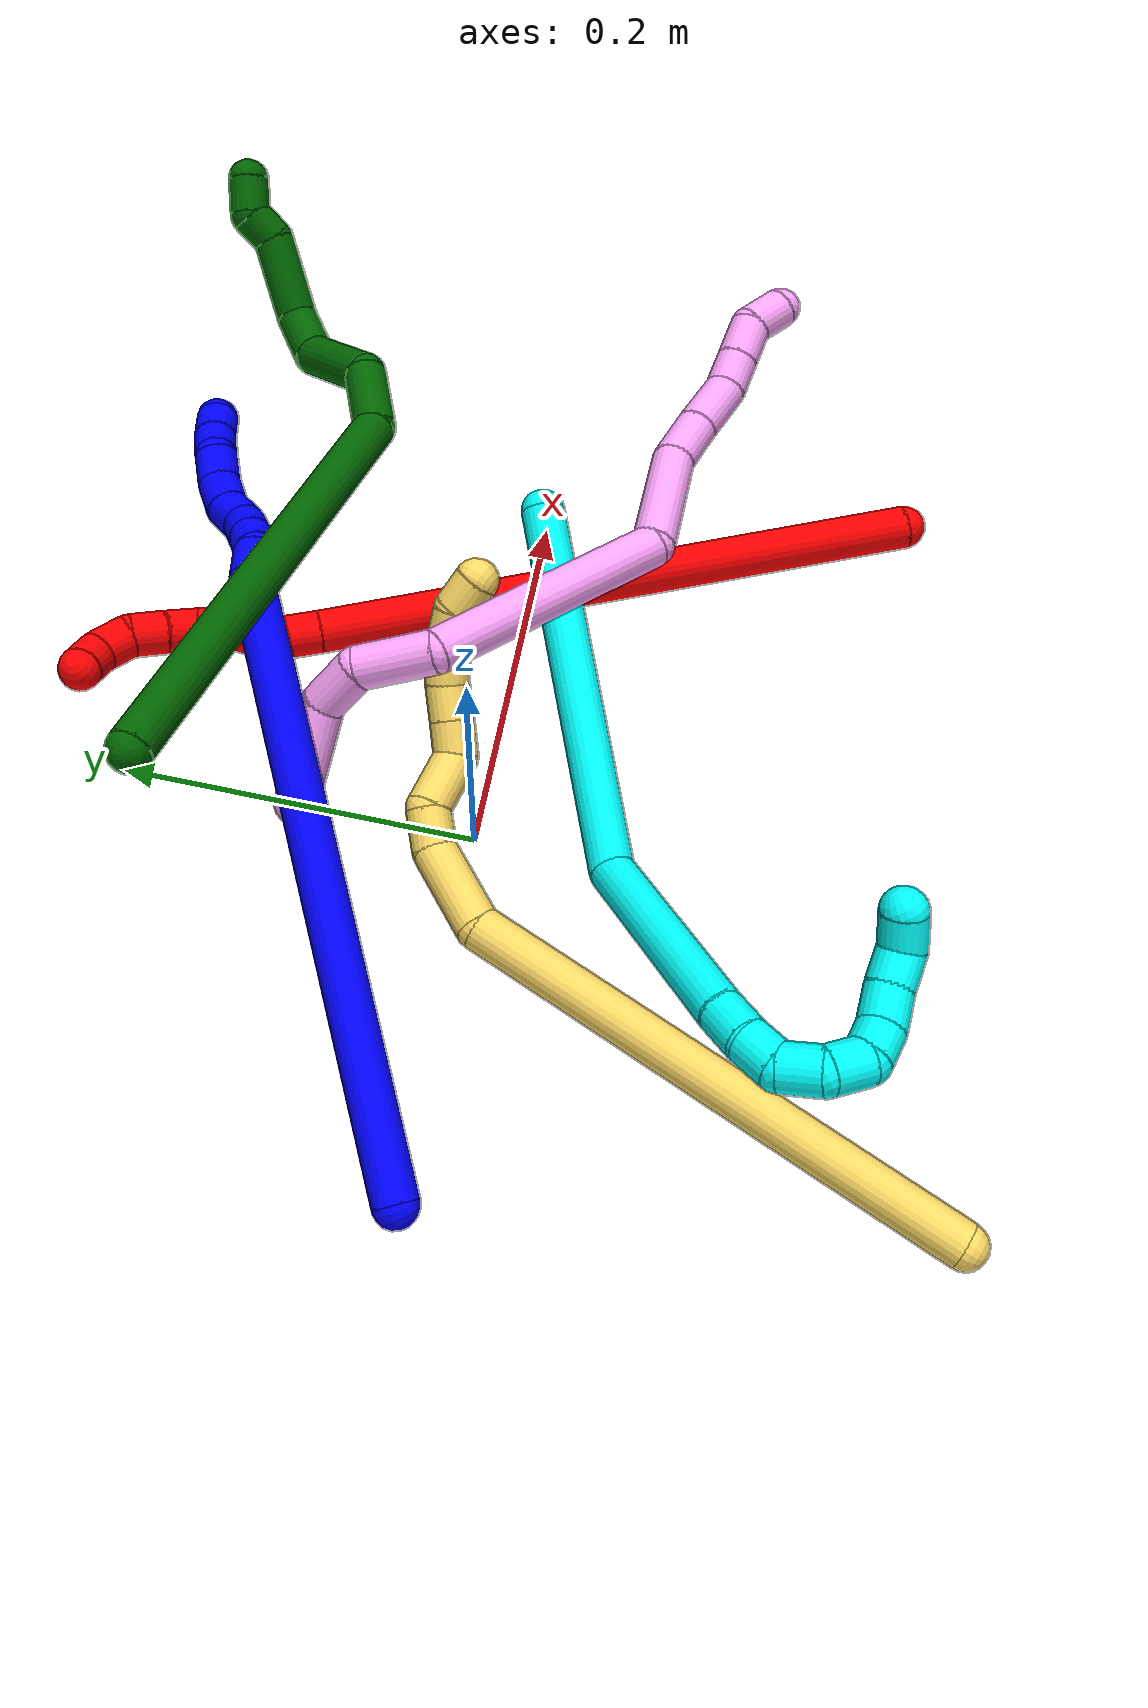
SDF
<sdf version="1.7">
 <world name="default">
  <plugin name="TubeGeneratorPlugin" filename="libtube_generator_plugin.so"/>
  <model name="photoneo_s_sensor">
   <static>1</static>
   <pose>0 0 2 1.57079 1.57079 3.14159</pose>
   <link name="link">
    <inertial><mass>0.1</mass></inertial>
    <sensor name="sensor" type="depth">
     <update_rate>30</update_rate>
     <camera>
      <horizontal_fov>1.22</horizontal_fov>
      <image><width>1920</width><height>1200</height><format>B8G8R8</format></image>
      <clip><near>0.1</near><far>4</far></clip>
      <depth_camera><output>points</output></depth_camera>
     </camera>
     <plugin name="camera_plugin" filename="libgazebo_ros_depth_camera.so">
      <baseline>0.2</baseline>
      <alwaysOn>1</alwaysOn>
      <updateRate>0.0</updateRate>
      <cameraName>camera_ir</cameraName>
      <imageTopicName>/camera/color/image_raw</imageTopicName>
      <cameraInfoTopicName>/camera/color/camera_info</cameraInfoTopicName>
      <depthImageTopicName>/camera/depth/image_raw</depthImageTopicName>
      <depthImageCameraInfoTopicName>/camera/depth/camera_info</depthImageCameraInfoTopicName>
      <pointCloudTopicName>/camera/depth/points</pointCloudTopicName>
      <frameName>fr_optical</frameName>
      <pointCloudCutoff>0.1</pointCloudCutoff>
      <pointCloudCutoffMax>2.0</pointCloudCutoffMax>
      <distortionK1>0</distortionK1>
      <distortionK2>0</distortionK2>
      <distortionK3>0</distortionK3>
      <distortionT1>0</distortionT1>
      <distortionT2>0</distortionT2>
      <CxPrime>0</CxPrime>
      <Cx>0</Cx>
      <Cy>0</Cy>
      <focalLength>0</focalLength>
      <hackBaseline>0</hackBaseline>
     </plugin>
    </sensor>
   </link>
  </model>
  <gravity>0 0 -9.8</gravity>
  <magnetic_field>6e-06 2.3e-05 -4.2e-05</magnetic_field>
  <atmosphere type="adiabatic"/>
  <physics name="default_physics" default="0" type="ode">
   <max_step_size>0.003</max_step_size>
   <real_time_factor>1</real_time_factor>
   <real_time_update_rate>1000</real_time_update_rate>
   <max_contacts>10000</max_contacts>
   <ode>
    <solver>
     <type>quick</type>
     <iters>100</iters>
     <sor>1.3</sor>
     <use_dynamic_moi_rescaling>0</use_dynamic_moi_rescaling>
    </solver>
    <constraints>
     <contact_max_correcting_vel>0</contact_max_correcting_vel>
     <contact_surface_layer>0.001</contact_surface_layer>
     <cfm>0</cfm>
     <erp>0.2</erp>
    </constraints>
   </ode>
  </physics>
  <scene><ambient>0.4 0.4 0.4 1</ambient><background>0.7 0.7 0.7 1</background><shadows>0</shadows></scene>
  <audio><device>default</device></audio>
  <spherical_coordinates>
   <surface_model>EARTH_WGS84</surface_model>
   <latitude_deg>0</latitude_deg>
   <longitude_deg>0</longitude_deg>
   <elevation>0</elevation>
   <heading_deg>0</heading_deg>
  </spherical_coordinates>
  <model name="bin">
   <static>1</static>
   <link name="bottom">
    <collision name="collision-bottom">
     <pose>0 0 -0.01 0 -0 0</pose>
     <geometry><box><size>0.8 0.6 0.02</size></box></geometry>
     <surface>
      <friction><ode><mu>100</mu><mu2>100</mu2></ode></friction>
      <contact><collide_bitmask>65535</collide_bitmask></contact>
     </surface>
    </collision>
   </link>
   <link name="west_wall">
    <collision name="collision-west_wall">
     <pose>-0.41 0 0.1 0 -0 0</pose>
     <geometry><box><size>0.02 0.6 0.2</size></box></geometry>
     <surface>
      <friction><ode><mu>100</mu><mu2>100</mu2></ode></friction>
      <contact><collide_bitmask>65535</collide_bitmask></contact>
     </surface>
    </collision>
   </link>
   <link name="east_wall">
    <collision name="collision-east_wall">
     <pose>0.41 0 0.1 0 -0 0</pose>
     <geometry><box><size>0.02 0.6 0.2</size></box></geometry>
     <surface>
      <friction><ode><mu>100</mu><mu2>100</mu2></ode></friction>
      <contact><collide_bitmask>65535</collide_bitmask></contact>
     </surface>
    </collision>
   </link>
   <link name="south_wall">
    <collision name="collision-south_wall">
     <pose>0 -0.31 0.1 0 -0 0</pose>
     <geometry><box><size>0.8 0.02 0.2</size></box></geometry>
     <surface>
      <friction><ode><mu>100</mu><mu2>100</mu2></ode></friction>
      <contact><collide_bitmask>65535</collide_bitmask></contact>
     </surface>
    </collision>
   </link>
   <link name="north_wall">
    <collision name="collision-north_wall">
     <pose>0 0.31 0.1 0 -0 0</pose>
     <geometry><box><size>0.8 0.02 0.2</size></box></geometry>
     <surface>
      <friction><ode><mu>100</mu><mu2>100</mu2></ode></friction>
      <contact><collide_bitmask>65535</collide_bitmask></contact>
     </surface>
    </collision>
   </link>
  </model>
  <model name="1">
   <static>0</static>
   <link name="1">
    <collision name="collision-cylinder-e_1_1_4">
     <pose>0.005703 0.054563 0.159133 -0.330314 0.033888 -0.005649</pose>
     <geometry><cylinder><radius>0.0125</radius><length>0.336648</length></cylinder></geometry>
     <surface>
      <friction><ode><mu>1.16</mu><mu2>1.16</mu2><slip1>0</slip1><slip2>0</slip2></ode></friction>
      <contact><ode><kp>1e+06</kp><kd>1</kd><max_vel>0</max_vel><min_depth>0.001</min_depth></ode></contact>
     </surface>
    </collision>
    <visual name="visual-cylinder-e_1_1_4">
     <pose>0.005703 0.054563 0.159133 -0.330314 0.033888 -0.005649</pose>
     <geometry><cylinder><radius>0.0125</radius><length>0.336648</length></cylinder></geometry>
     <material><ambient>0 0 1 1</ambient></material>
    </visual>
    <collision name="collision-cylinder-e_2_4_5">
     <pose>0.012825 0.117011 0.325495 -0.828823 0.131842 -0.058063</pose>
     <geometry><cylinder><radius>0.0125</radius><length>0.021581</length></cylinder></geometry>
     <surface>
      <friction><ode><mu>1.16</mu><mu2>1.16</mu2><slip1>0</slip1><slip2>0</slip2></ode></friction>
      <contact><ode><kp>1e+06</kp><kd>1</kd><max_vel>0</max_vel><min_depth>0.001</min_depth></ode></contact>
     </surface>
    </collision>
    <visual name="visual-cylinder-e_2_4_5">
     <pose>0.012825 0.117011 0.325495 -0.828823 0.131842 -0.058063</pose>
     <geometry><cylinder><radius>0.0125</radius><length>0.021581</length></cylinder></geometry>
     <material><ambient>0 0 1 1</ambient></material>
    </visual>
    <collision name="collision-cylinder-e_3_5_6">
     <pose>0.011484 0.133621 0.337574 -1.06334 -0.269678 0.159245</pose>
     <geometry><cylinder><radius>0.0125</radius><length>0.020715</length></cylinder></geometry>
     <surface>
      <friction><ode><mu>1.16</mu><mu2>1.16</mu2><slip1>0</slip1><slip2>0</slip2></ode></friction>
      <contact><ode><kp>1e+06</kp><kd>1</kd><max_vel>0</max_vel><min_depth>0.001</min_depth></ode></contact>
     </surface>
    </collision>
    <visual name="visual-cylinder-e_3_5_6">
     <pose>0.011484 0.133621 0.337574 -1.06334 -0.269678 0.159245</pose>
     <geometry><cylinder><radius>0.0125</radius><length>0.020715</length></cylinder></geometry>
     <material><ambient>0 0 1 1</ambient></material>
    </visual>
    <collision name="collision-cylinder-e_4_6_7">
     <pose>0.005504 0.150555 0.34721 -1.04313 -0.326776 0.188903</pose>
     <geometry><cylinder><radius>0.0125</radius><length>0.020066</length></cylinder></geometry>
     <surface>
      <friction><ode><mu>1.16</mu><mu2>1.16</mu2><slip1>0</slip1><slip2>0</slip2></ode></friction>
      <contact><ode><kp>1e+06</kp><kd>1</kd><max_vel>0</max_vel><min_depth>0.001</min_depth></ode></contact>
     </surface>
    </collision>
    <visual name="visual-cylinder-e_4_6_7">
     <pose>0.005504 0.150555 0.34721 -1.04313 -0.326776 0.188903</pose>
     <geometry><cylinder><radius>0.0125</radius><length>0.020066</length></cylinder></geometry>
     <material><ambient>0 0 1 1</ambient></material>
    </visual>
    <collision name="collision-cylinder-e_5_7_8">
     <pose>-0.002696 0.164906 0.358583 -0.750225 -0.505043 0.202507</pose>
     <geometry><cylinder><radius>0.0125</radius><length>0.020583</length></cylinder></geometry>
     <surface>
      <friction><ode><mu>1.16</mu><mu2>1.16</mu2><slip1>0</slip1><slip2>0</slip2></ode></friction>
      <contact><ode><kp>1e+06</kp><kd>1</kd><max_vel>0</max_vel><min_depth>0.001</min_depth></ode></contact>
     </surface>
    </collision>
    <visual name="visual-cylinder-e_5_7_8">
     <pose>-0.002696 0.164906 0.358583 -0.750225 -0.505043 0.202507</pose>
     <geometry><cylinder><radius>0.0125</radius><length>0.020583</length></cylinder></geometry>
     <material><ambient>0 0 1 1</ambient></material>
    </visual>
    <collision name="collision-cylinder-e_6_8_9">
     <pose>-0.009244 0.176951 0.373323 -0.626921 -0.154556 0.050188</pose>
     <geometry><cylinder><radius>0.0125</radius><length>0.020372</length></cylinder></geometry>
     <surface>
      <friction><ode><mu>1.16</mu><mu2>1.16</mu2><slip1>0</slip1><slip2>0</slip2></ode></friction>
      <contact><ode><kp>1e+06</kp><kd>1</kd><max_vel>0</max_vel><min_depth>0.001</min_depth></ode></contact>
     </surface>
    </collision>
    <visual name="visual-cylinder-e_6_8_9">
     <pose>-0.009244 0.176951 0.373323 -0.626921 -0.154556 0.050188</pose>
     <geometry><cylinder><radius>0.0125</radius><length>0.020372</length></cylinder></geometry>
     <material><ambient>0 0 1 1</ambient></material>
    </visual>
    <collision name="collision-cylinder-e_7_9_10">
     <pose>-0.010248 0.187802 0.390148 -0.518202 0.056453 -0.014967</pose>
     <geometry><cylinder><radius>0.0125</radius><length>0.020003</length></cylinder></geometry>
     <surface>
      <friction><ode><mu>1.16</mu><mu2>1.16</mu2><slip1>0</slip1><slip2>0</slip2></ode></friction>
      <contact><ode><kp>1e+06</kp><kd>1</kd><max_vel>0</max_vel><min_depth>0.001</min_depth></ode></contact>
     </surface>
    </collision>
    <visual name="visual-cylinder-e_7_9_10">
     <pose>-0.010248 0.187802 0.390148 -0.518202 0.056453 -0.014967</pose>
     <geometry><cylinder><radius>0.0125</radius><length>0.020003</length></cylinder></geometry>
     <material><ambient>0 0 1 1</ambient></material>
    </visual>
    <collision name="collision-cylinder-e_8_10_11">
     <pose>-0.010796 0.200809 0.404636 -0.946002 -0.111456 0.057081</pose>
     <geometry><cylinder><radius>0.0125</radius><length>0.020002</length></cylinder></geometry>
     <surface>
      <friction><ode><mu>1.16</mu><mu2>1.16</mu2><slip1>0</slip1><slip2>0</slip2></ode></friction>
      <contact><ode><kp>1e+06</kp><kd>1</kd><max_vel>0</max_vel><min_depth>0.001</min_depth></ode></contact>
     </surface>
    </collision>
    <visual name="visual-cylinder-e_8_10_11">
     <pose>-0.010796 0.200809 0.404636 -0.946002 -0.111456 0.057081</pose>
     <geometry><cylinder><radius>0.0125</radius><length>0.020002</length></cylinder></geometry>
     <material><ambient>0 0 1 1</ambient></material>
    </visual>
    <collision name="collision-cylinder-e_9_11_2">
     <pose>-0.011468 0.216747 0.416619 -0.906298 0.043934 -0.021396</pose>
     <geometry><cylinder><radius>0.0125</radius><length>0.020031</length></cylinder></geometry>
     <surface>
      <friction><ode><mu>1.16</mu><mu2>1.16</mu2><slip1>0</slip1><slip2>0</slip2></ode></friction>
      <contact><ode><kp>1e+06</kp><kd>1</kd><max_vel>0</max_vel><min_depth>0.001</min_depth></ode></contact>
     </surface>
    </collision>
    <visual name="visual-cylinder-e_9_11_2">
     <pose>-0.011468 0.216747 0.416619 -0.906298 0.043934 -0.021396</pose>
     <geometry><cylinder><radius>0.0125</radius><length>0.020031</length></cylinder></geometry>
     <material><ambient>0 0 1 1</ambient></material>
    </visual>
    <collision name="collision-sphere-2">
     <pose>-0.011028 0.224623 0.42279 0 -0 0</pose>
     <geometry><sphere><radius>0.0125</radius></sphere></geometry>
     <surface>
      <friction><ode><mu>1.16</mu><mu2>1.16</mu2><slip1>0</slip1><slip2>0</slip2></ode></friction>
      <contact><ode><kp>1e+06</kp><kd>1</kd><max_vel>0</max_vel><min_depth>0.001</min_depth></ode></contact>
     </surface>
    </collision>
    <visual name="visual-sphere-2">
     <pose>-0.011028 0.224623 0.42279 0 -0 0</pose>
     <geometry><sphere><radius>0.0125</radius></sphere></geometry>
     <material><ambient>0 0 1 1</ambient></material>
    </visual>
    <collision name="collision-sphere-11">
     <pose>-0.011908 0.20887 0.410449 0 -0 0</pose>
     <geometry><sphere><radius>0.0125</radius></sphere></geometry>
     <surface>
      <friction><ode><mu>1.16</mu><mu2>1.16</mu2><slip1>0</slip1><slip2>0</slip2></ode></friction>
      <contact><ode><kp>1e+06</kp><kd>1</kd><max_vel>0</max_vel><min_depth>0.001</min_depth></ode></contact>
     </surface>
    </collision>
    <visual name="visual-sphere-11">
     <pose>-0.011908 0.20887 0.410449 0 -0 0</pose>
     <geometry><sphere><radius>0.0125</radius></sphere></geometry>
     <material><ambient>0 0 1 1</ambient></material>
    </visual>
    <collision name="collision-sphere-10">
     <pose>-0.009683 0.192748 0.398822 0 -0 0</pose>
     <geometry><sphere><radius>0.0125</radius></sphere></geometry>
     <surface>
      <friction><ode><mu>1.16</mu><mu2>1.16</mu2><slip1>0</slip1><slip2>0</slip2></ode></friction>
      <contact><ode><kp>1e+06</kp><kd>1</kd><max_vel>0</max_vel><min_depth>0.001</min_depth></ode></contact>
     </surface>
    </collision>
    <visual name="visual-sphere-10">
     <pose>-0.009683 0.192748 0.398822 0 -0 0</pose>
     <geometry><sphere><radius>0.0125</radius></sphere></geometry>
     <material><ambient>0 0 1 1</ambient></material>
    </visual>
    <collision name="collision-sphere-9">
     <pose>-0.010812 0.182856 0.381473 0 -0 0</pose>
     <geometry><sphere><radius>0.0125</radius></sphere></geometry>
     <surface>
      <friction><ode><mu>1.16</mu><mu2>1.16</mu2><slip1>0</slip1><slip2>0</slip2></ode></friction>
      <contact><ode><kp>1e+06</kp><kd>1</kd><max_vel>0</max_vel><min_depth>0.001</min_depth></ode></contact>
     </surface>
    </collision>
    <visual name="visual-sphere-9">
     <pose>-0.010812 0.182856 0.381473 0 -0 0</pose>
     <geometry><sphere><radius>0.0125</radius></sphere></geometry>
     <material><ambient>0 0 1 1</ambient></material>
    </visual>
    <collision name="collision-sphere-4">
     <pose>0.011406 0.109126 0.318266 0 -0 0</pose>
     <geometry><sphere><radius>0.0125</radius></sphere></geometry>
     <surface>
      <friction><ode><mu>1.16</mu><mu2>1.16</mu2><slip1>0</slip1><slip2>0</slip2></ode></friction>
      <contact><ode><kp>1e+06</kp><kd>1</kd><max_vel>0</max_vel><min_depth>0.001</min_depth></ode></contact>
     </surface>
    </collision>
    <visual name="visual-sphere-4">
     <pose>0.011406 0.109126 0.318266 0 -0 0</pose>
     <geometry><sphere><radius>0.0125</radius></sphere></geometry>
     <material><ambient>0 0 1 1</ambient></material>
    </visual>
    <collision name="collision-sphere-1">
     <geometry><sphere><radius>0.0125</radius></sphere></geometry>
     <surface>
      <friction><ode><mu>1.16</mu><mu2>1.16</mu2><slip1>0</slip1><slip2>0</slip2></ode></friction>
      <contact><ode><kp>1e+06</kp><kd>1</kd><max_vel>0</max_vel><min_depth>0.001</min_depth></ode></contact>
     </surface>
    </collision>
    <visual name="visual-sphere-1">
     <geometry><sphere><radius>0.0125</radius></sphere></geometry>
     <material><ambient>0 0 1 1</ambient></material>
    </visual>
    <collision name="collision-sphere-8">
     <pose>-0.007676 0.171047 0.365172 0 -0 0</pose>
     <geometry><sphere><radius>0.0125</radius></sphere></geometry>
     <surface>
      <friction><ode><mu>1.16</mu><mu2>1.16</mu2><slip1>0</slip1><slip2>0</slip2></ode></friction>
      <contact><ode><kp>1e+06</kp><kd>1</kd><max_vel>0</max_vel><min_depth>0.001</min_depth></ode></contact>
     </surface>
    </collision>
    <visual name="visual-sphere-8">
     <pose>-0.007676 0.171047 0.365172 0 -0 0</pose>
     <geometry><sphere><radius>0.0125</radius></sphere></geometry>
     <material><ambient>0 0 1 1</ambient></material>
    </visual>
    <collision name="collision-sphere-5">
     <pose>0.014243 0.124896 0.332723 0 -0 0</pose>
     <geometry><sphere><radius>0.0125</radius></sphere></geometry>
     <surface>
      <friction><ode><mu>1.16</mu><mu2>1.16</mu2><slip1>0</slip1><slip2>0</slip2></ode></friction>
      <contact><ode><kp>1e+06</kp><kd>1</kd><max_vel>0</max_vel><min_depth>0.001</min_depth></ode></contact>
     </surface>
    </collision>
    <visual name="visual-sphere-5">
     <pose>0.014243 0.124896 0.332723 0 -0 0</pose>
     <geometry><sphere><radius>0.0125</radius></sphere></geometry>
     <material><ambient>0 0 1 1</ambient></material>
    </visual>
    <collision name="collision-sphere-6">
     <pose>0.008724 0.142346 0.342426 0 -0 0</pose>
     <geometry><sphere><radius>0.0125</radius></sphere></geometry>
     <surface>
      <friction><ode><mu>1.16</mu><mu2>1.16</mu2><slip1>0</slip1><slip2>0</slip2></ode></friction>
      <contact><ode><kp>1e+06</kp><kd>1</kd><max_vel>0</max_vel><min_depth>0.001</min_depth></ode></contact>
     </surface>
    </collision>
    <visual name="visual-sphere-6">
     <pose>0.008724 0.142346 0.342426 0 -0 0</pose>
     <geometry><sphere><radius>0.0125</radius></sphere></geometry>
     <material><ambient>0 0 1 1</ambient></material>
    </visual>
    <collision name="collision-sphere-7">
     <pose>0.002283 0.158765 0.351994 0 -0 0</pose>
     <geometry><sphere><radius>0.0125</radius></sphere></geometry>
     <surface>
      <friction><ode><mu>1.16</mu><mu2>1.16</mu2><slip1>0</slip1><slip2>0</slip2></ode></friction>
      <contact><ode><kp>1e+06</kp><kd>1</kd><max_vel>0</max_vel><min_depth>0.001</min_depth></ode></contact>
     </surface>
    </collision>
    <visual name="visual-sphere-7">
     <pose>0.002283 0.158765 0.351994 0 -0 0</pose>
     <geometry><sphere><radius>0.0125</radius></sphere></geometry>
     <material><ambient>0 0 1 1</ambient></material>
    </visual>
    <inertial>
     <pose>0.003301 0.091593 0.22757 0 -0 0</pose>
     <mass>0.5</mass>
     <inertia>
      <ixx>0.003184</ixx>
      <ixy>0</ixy>
      <ixz>0</ixz>
      <iyy>0.003029</iyy>
      <iyz>0</iyz>
      <izz>-0.001117</izz>
     </inertia>
    </inertial>
   </link>
   <pose>-0.198157 -0.004172 0.011854 -1.0748 -0.347814 -1.12847</pose>
  </model>
  <model name="2">
   <static>0</static>
   <link name="2">
    <collision name="collision-cylinder-e_1_1_4">
     <pose>-0.096995 0.141886 0.027193 -1.38144 -0.591267 0.493214</pose>
     <geometry><cylinder><radius>0.0125</radius><length>0.348017</length></cylinder></geometry>
     <surface>
      <friction><ode><mu>1.16</mu><mu2>1.16</mu2><slip1>0</slip1><slip2>0</slip2></ode></friction>
      <contact><ode><kp>1e+06</kp><kd>1</kd><max_vel>0</max_vel><min_depth>0.001</min_depth></ode></contact>
     </surface>
    </collision>
    <visual name="visual-cylinder-e_1_1_4">
     <pose>-0.096995 0.141886 0.027193 -1.38144 -0.591267 0.493214</pose>
     <geometry><cylinder><radius>0.0125</radius><length>0.348017</length></cylinder></geometry>
     <material><ambient>1 0 0 1</ambient></material>
    </visual>
    <collision name="collision-cylinder-e_2_4_5">
     <pose>-0.202169 0.295216 0.058018 -1.26355 -0.598044 0.443768</pose>
     <geometry><cylinder><radius>0.0125</radius><length>0.029057</length></cylinder></geometry>
     <surface>
      <friction><ode><mu>1.16</mu><mu2>1.16</mu2><slip1>0</slip1><slip2>0</slip2></ode></friction>
      <contact><ode><kp>1e+06</kp><kd>1</kd><max_vel>0</max_vel><min_depth>0.001</min_depth></ode></contact>
     </surface>
    </collision>
    <visual name="visual-cylinder-e_2_4_5">
     <pose>-0.202169 0.295216 0.058018 -1.26355 -0.598044 0.443768</pose>
     <geometry><cylinder><radius>0.0125</radius><length>0.029057</length></cylinder></geometry>
     <material><ambient>1 0 0 1</ambient></material>
    </visual>
    <collision name="collision-cylinder-e_3_5_6">
     <pose>-0.211727 0.317009 0.06589 -1.18187 -0.122598 0.082308</pose>
     <geometry><cylinder><radius>0.0125</radius><length>0.022537</length></cylinder></geometry>
     <surface>
      <friction><ode><mu>1.16</mu><mu2>1.16</mu2><slip1>0</slip1><slip2>0</slip2></ode></friction>
      <contact><ode><kp>1e+06</kp><kd>1</kd><max_vel>0</max_vel><min_depth>0.001</min_depth></ode></contact>
     </surface>
    </collision>
    <visual name="visual-cylinder-e_3_5_6">
     <pose>-0.211727 0.317009 0.06589 -1.18187 -0.122598 0.082308</pose>
     <geometry><cylinder><radius>0.0125</radius><length>0.022537</length></cylinder></geometry>
     <material><ambient>1 0 0 1</ambient></material>
    </visual>
    <collision name="collision-cylinder-e_4_6_7">
     <pose>-0.216669 0.3367 0.068969 -1.69459 -0.36187 0.408443</pose>
     <geometry><cylinder><radius>0.0125</radius><length>0.020131</length></cylinder></geometry>
     <surface>
      <friction><ode><mu>1.16</mu><mu2>1.16</mu2><slip1>0</slip1><slip2>0</slip2></ode></friction>
      <contact><ode><kp>1e+06</kp><kd>1</kd><max_vel>0</max_vel><min_depth>0.001</min_depth></ode></contact>
     </surface>
    </collision>
    <visual name="visual-cylinder-e_4_6_7">
     <pose>-0.216669 0.3367 0.068969 -1.69459 -0.36187 0.408443</pose>
     <geometry><cylinder><radius>0.0125</radius><length>0.020131</length></cylinder></geometry>
     <material><ambient>1 0 0 1</ambient></material>
    </visual>
    <collision name="collision-cylinder-e_5_7_8">
     <pose>-0.225619 0.352929 0.072687 -0.954333 -0.567995 0.299559</pose>
     <geometry><cylinder><radius>0.0125</radius><length>0.020029</length></cylinder></geometry>
     <surface>
      <friction><ode><mu>1.16</mu><mu2>1.16</mu2><slip1>0</slip1><slip2>0</slip2></ode></friction>
      <contact><ode><kp>1e+06</kp><kd>1</kd><max_vel>0</max_vel><min_depth>0.001</min_depth></ode></contact>
     </surface>
    </collision>
    <visual name="visual-cylinder-e_5_7_8">
     <pose>-0.225619 0.352929 0.072687 -0.954333 -0.567995 0.299559</pose>
     <geometry><cylinder><radius>0.0125</radius><length>0.020029</length></cylinder></geometry>
     <material><ambient>1 0 0 1</ambient></material>
    </visual>
    <collision name="collision-cylinder-e_6_8_9">
     <pose>-0.236511 0.367056 0.081752 -1.04669 -0.582209 0.342379</pose>
     <geometry><cylinder><radius>0.0125</radius><length>0.02002</length></cylinder></geometry>
     <surface>
      <friction><ode><mu>1.16</mu><mu2>1.16</mu2><slip1>0</slip1><slip2>0</slip2></ode></friction>
      <contact><ode><kp>1e+06</kp><kd>1</kd><max_vel>0</max_vel><min_depth>0.001</min_depth></ode></contact>
     </surface>
    </collision>
    <visual name="visual-cylinder-e_6_8_9">
     <pose>-0.236511 0.367056 0.081752 -1.04669 -0.582209 0.342379</pose>
     <geometry><cylinder><radius>0.0125</radius><length>0.02002</length></cylinder></geometry>
     <material><ambient>1 0 0 1</ambient></material>
    </visual>
    <collision name="collision-cylinder-e_7_9_10">
     <pose>-0.250334 0.37913 0.088871 -1.02536 -0.973641 0.57913</pose>
     <geometry><cylinder><radius>0.0125</radius><length>0.020121</length></cylinder></geometry>
     <surface>
      <friction><ode><mu>1.16</mu><mu2>1.16</mu2><slip1>0</slip1><slip2>0</slip2></ode></friction>
      <contact><ode><kp>1e+06</kp><kd>1</kd><max_vel>0</max_vel><min_depth>0.001</min_depth></ode></contact>
     </surface>
    </collision>
    <visual name="visual-cylinder-e_7_9_10">
     <pose>-0.250334 0.37913 0.088871 -1.02536 -0.973641 0.57913</pose>
     <geometry><cylinder><radius>0.0125</radius><length>0.020121</length></cylinder></geometry>
     <material><ambient>1 0 0 1</ambient></material>
    </visual>
    <collision name="collision-cylinder-e_8_10_2">
     <pose>-0.265964 0.382803 0.098594 0.169744 -0.815198 -0.073435</pose>
     <geometry><cylinder><radius>0.0125</radius><length>0.020088</length></cylinder></geometry>
     <surface>
      <friction><ode><mu>1.16</mu><mu2>1.16</mu2><slip1>0</slip1><slip2>0</slip2></ode></friction>
      <contact><ode><kp>1e+06</kp><kd>1</kd><max_vel>0</max_vel><min_depth>0.001</min_depth></ode></contact>
     </surface>
    </collision>
    <visual name="visual-cylinder-e_8_10_2">
     <pose>-0.265964 0.382803 0.098594 0.169744 -0.815198 -0.073435</pose>
     <geometry><cylinder><radius>0.0125</radius><length>0.020088</length></cylinder></geometry>
     <material><ambient>1 0 0 1</ambient></material>
    </visual>
    <collision name="collision-sphere-2">
     <pose>-0.273275 0.38164 0.105382 0 -0 0</pose>
     <geometry><sphere><radius>0.0125</radius></sphere></geometry>
     <surface>
      <friction><ode><mu>1.16</mu><mu2>1.16</mu2><slip1>0</slip1><slip2>0</slip2></ode></friction>
      <contact><ode><kp>1e+06</kp><kd>1</kd><max_vel>0</max_vel><min_depth>0.001</min_depth></ode></contact>
     </surface>
    </collision>
    <visual name="visual-sphere-2">
     <pose>-0.273275 0.38164 0.105382 0 -0 0</pose>
     <geometry><sphere><radius>0.0125</radius></sphere></geometry>
     <material><ambient>1 0 0 1</ambient></material>
    </visual>
    <collision name="collision-sphere-10">
     <pose>-0.258654 0.383967 0.091806 0 -0 0</pose>
     <geometry><sphere><radius>0.0125</radius></sphere></geometry>
     <surface>
      <friction><ode><mu>1.16</mu><mu2>1.16</mu2><slip1>0</slip1><slip2>0</slip2></ode></friction>
      <contact><ode><kp>1e+06</kp><kd>1</kd><max_vel>0</max_vel><min_depth>0.001</min_depth></ode></contact>
     </surface>
    </collision>
    <visual name="visual-sphere-10">
     <pose>-0.258654 0.383967 0.091806 0 -0 0</pose>
     <geometry><sphere><radius>0.0125</radius></sphere></geometry>
     <material><ambient>1 0 0 1</ambient></material>
    </visual>
    <collision name="collision-sphere-9">
     <pose>-0.242015 0.374294 0.085936 0 -0 0</pose>
     <geometry><sphere><radius>0.0125</radius></sphere></geometry>
     <surface>
      <friction><ode><mu>1.16</mu><mu2>1.16</mu2><slip1>0</slip1><slip2>0</slip2></ode></friction>
      <contact><ode><kp>1e+06</kp><kd>1</kd><max_vel>0</max_vel><min_depth>0.001</min_depth></ode></contact>
     </surface>
    </collision>
    <visual name="visual-sphere-9">
     <pose>-0.242015 0.374294 0.085936 0 -0 0</pose>
     <geometry><sphere><radius>0.0125</radius></sphere></geometry>
     <material><ambient>1 0 0 1</ambient></material>
    </visual>
    <collision name="collision-sphere-4">
     <pose>-0.193989 0.283771 0.054387 0 -0 0</pose>
     <geometry><sphere><radius>0.0125</radius></sphere></geometry>
     <surface>
      <friction><ode><mu>1.16</mu><mu2>1.16</mu2><slip1>0</slip1><slip2>0</slip2></ode></friction>
      <contact><ode><kp>1e+06</kp><kd>1</kd><max_vel>0</max_vel><min_depth>0.001</min_depth></ode></contact>
     </surface>
    </collision>
    <visual name="visual-sphere-4">
     <pose>-0.193989 0.283771 0.054387 0 -0 0</pose>
     <geometry><sphere><radius>0.0125</radius></sphere></geometry>
     <material><ambient>1 0 0 1</ambient></material>
    </visual>
    <collision name="collision-sphere-1">
     <geometry><sphere><radius>0.0125</radius></sphere></geometry>
     <surface>
      <friction><ode><mu>1.16</mu><mu2>1.16</mu2><slip1>0</slip1><slip2>0</slip2></ode></friction>
      <contact><ode><kp>1e+06</kp><kd>1</kd><max_vel>0</max_vel><min_depth>0.001</min_depth></ode></contact>
     </surface>
    </collision>
    <visual name="visual-sphere-1">
     <geometry><sphere><radius>0.0125</radius></sphere></geometry>
     <material><ambient>1 0 0 1</ambient></material>
    </visual>
    <collision name="collision-sphere-8">
     <pose>-0.231007 0.359817 0.077568 0 -0 0</pose>
     <geometry><sphere><radius>0.0125</radius></sphere></geometry>
     <surface>
      <friction><ode><mu>1.16</mu><mu2>1.16</mu2><slip1>0</slip1><slip2>0</slip2></ode></friction>
      <contact><ode><kp>1e+06</kp><kd>1</kd><max_vel>0</max_vel><min_depth>0.001</min_depth></ode></contact>
     </surface>
    </collision>
    <visual name="visual-sphere-8">
     <pose>-0.231007 0.359817 0.077568 0 -0 0</pose>
     <geometry><sphere><radius>0.0125</radius></sphere></geometry>
     <material><ambient>1 0 0 1</ambient></material>
    </visual>
    <collision name="collision-sphere-5">
     <pose>-0.210349 0.30666 0.061649 0 -0 0</pose>
     <geometry><sphere><radius>0.0125</radius></sphere></geometry>
     <surface>
      <friction><ode><mu>1.16</mu><mu2>1.16</mu2><slip1>0</slip1><slip2>0</slip2></ode></friction>
      <contact><ode><kp>1e+06</kp><kd>1</kd><max_vel>0</max_vel><min_depth>0.001</min_depth></ode></contact>
     </surface>
    </collision>
    <visual name="visual-sphere-5">
     <pose>-0.210349 0.30666 0.061649 0 -0 0</pose>
     <geometry><sphere><radius>0.0125</radius></sphere></geometry>
     <material><ambient>1 0 0 1</ambient></material>
    </visual>
    <collision name="collision-sphere-6">
     <pose>-0.213105 0.327358 0.070131 0 -0 0</pose>
     <geometry><sphere><radius>0.0125</radius></sphere></geometry>
     <surface>
      <friction><ode><mu>1.16</mu><mu2>1.16</mu2><slip1>0</slip1><slip2>0</slip2></ode></friction>
      <contact><ode><kp>1e+06</kp><kd>1</kd><max_vel>0</max_vel><min_depth>0.001</min_depth></ode></contact>
     </surface>
    </collision>
    <visual name="visual-sphere-6">
     <pose>-0.213105 0.327358 0.070131 0 -0 0</pose>
     <geometry><sphere><radius>0.0125</radius></sphere></geometry>
     <material><ambient>1 0 0 1</ambient></material>
    </visual>
    <collision name="collision-sphere-7">
     <pose>-0.220232 0.346041 0.067806 0 -0 0</pose>
     <geometry><sphere><radius>0.0125</radius></sphere></geometry>
     <surface>
      <friction><ode><mu>1.16</mu><mu2>1.16</mu2><slip1>0</slip1><slip2>0</slip2></ode></friction>
      <contact><ode><kp>1e+06</kp><kd>1</kd><max_vel>0</max_vel><min_depth>0.001</min_depth></ode></contact>
     </surface>
    </collision>
    <visual name="visual-sphere-7">
     <pose>-0.220232 0.346041 0.067806 0 -0 0</pose>
     <geometry><sphere><radius>0.0125</radius></sphere></geometry>
     <material><ambient>1 0 0 1</ambient></material>
    </visual>
    <inertial>
     <pose>-0.136794 0.203229 0.041768 0 -0 0</pose>
     <mass>0.5</mass>
     <inertia>
      <ixx>0.003956</ixx>
      <ixy>0</ixy>
      <ixz>0</ixz>
      <iyy>0.002924</iyy>
      <iyz>0</iyz>
      <izz>-0.000903</izz>
     </inertia>
    </inertial>
   </link>
   <pose>0.239835 -0.206436 0.013016 -0.104419 -0.13346 -0.18892</pose>
  </model>
  <model name="3">
   <static>0</static>
   <link name="3">
    <collision name="collision-cylinder-e_1_1_4">
     <pose>-0.053777 -0.008825 -0.090783 3.04469 -0.532731 -2.78984</pose>
     <geometry><cylinder><radius>0.0125</radius><length>0.211769</length></cylinder></geometry>
     <surface>
      <friction><ode><mu>1.16</mu><mu2>1.16</mu2><slip1>0</slip1><slip2>0</slip2></ode></friction>
      <contact><ode><kp>1e+06</kp><kd>1</kd><max_vel>0</max_vel><min_depth>0.001</min_depth></ode></contact>
     </surface>
    </collision>
    <visual name="visual-cylinder-e_1_1_4">
     <pose>-0.053777 -0.008825 -0.090783 3.04469 -0.532731 -2.78984</pose>
     <geometry><cylinder><radius>0.0125</radius><length>0.211769</length></cylinder></geometry>
     <material><ambient>0.003922 1 0.996078 1</ambient></material>
    </visual>
    <collision name="collision-cylinder-e_2_4_5">
     <pose>-0.142018 -0.058811 -0.209303 2.16375 -0.606918 -1.06397</pose>
     <geometry><cylinder><radius>0.0125</radius><length>0.120851</length></cylinder></geometry>
     <surface>
      <friction><ode><mu>1.16</mu><mu2>1.16</mu2><slip1>0</slip1><slip2>0</slip2></ode></friction>
      <contact><ode><kp>1e+06</kp><kd>1</kd><max_vel>0</max_vel><min_depth>0.001</min_depth></ode></contact>
     </surface>
    </collision>
    <visual name="visual-cylinder-e_2_4_5">
     <pose>-0.142018 -0.058811 -0.209303 2.16375 -0.606918 -1.06397</pose>
     <geometry><cylinder><radius>0.0125</radius><length>0.120851</length></cylinder></geometry>
     <material><ambient>0.003922 1 0.996078 1</ambient></material>
    </visual>
    <collision name="collision-cylinder-e_3_5_6">
     <pose>-0.181905 -0.107711 -0.24265 2.1981 -0.516157 -0.954958</pose>
     <geometry><cylinder><radius>0.0125</radius><length>0.021981</length></cylinder></geometry>
     <surface>
      <friction><ode><mu>1.16</mu><mu2>1.16</mu2><slip1>0</slip1><slip2>0</slip2></ode></friction>
      <contact><ode><kp>1e+06</kp><kd>1</kd><max_vel>0</max_vel><min_depth>0.001</min_depth></ode></contact>
     </surface>
    </collision>
    <visual name="visual-cylinder-e_3_5_6">
     <pose>-0.181905 -0.107711 -0.24265 2.1981 -0.516157 -0.954958</pose>
     <geometry><cylinder><radius>0.0125</radius><length>0.021981</length></cylinder></geometry>
     <material><ambient>0.003922 1 0.996078 1</ambient></material>
    </visual>
    <collision name="collision-cylinder-e_4_6_7">
     <pose>-0.190582 -0.12287 -0.254459 2.26669 -0.324521 -0.673404</pose>
     <geometry><cylinder><radius>0.0125</radius><length>0.020401</length></cylinder></geometry>
     <surface>
      <friction><ode><mu>1.16</mu><mu2>1.16</mu2><slip1>0</slip1><slip2>0</slip2></ode></friction>
      <contact><ode><kp>1e+06</kp><kd>1</kd><max_vel>0</max_vel><min_depth>0.001</min_depth></ode></contact>
     </surface>
    </collision>
    <visual name="visual-cylinder-e_4_6_7">
     <pose>-0.190582 -0.12287 -0.254459 2.26669 -0.324521 -0.673404</pose>
     <geometry><cylinder><radius>0.0125</radius><length>0.020401</length></cylinder></geometry>
     <material><ambient>0.003922 1 0.996078 1</ambient></material>
    </visual>
    <collision name="collision-cylinder-e_5_7_8">
     <pose>-0.190947 -0.14022 -0.264964 1.98006 0.26072 0.394353</pose>
     <geometry><cylinder><radius>0.0125</radius><length>0.022406</length></cylinder></geometry>
     <surface>
      <friction><ode><mu>1.16</mu><mu2>1.16</mu2><slip1>0</slip1><slip2>0</slip2></ode></friction>
      <contact><ode><kp>1e+06</kp><kd>1</kd><max_vel>0</max_vel><min_depth>0.001</min_depth></ode></contact>
     </surface>
    </collision>
    <visual name="visual-cylinder-e_5_7_8">
     <pose>-0.190947 -0.14022 -0.264964 1.98006 0.26072 0.394353</pose>
     <geometry><cylinder><radius>0.0125</radius><length>0.022406</length></cylinder></geometry>
     <material><ambient>0.003922 1 0.996078 1</ambient></material>
    </visual>
    <collision name="collision-cylinder-e_6_8_9">
     <pose>-0.179643 -0.155851 -0.272602 2.09956 0.905601 1.40633</pose>
     <geometry><cylinder><radius>0.0125</radius><length>0.021393</length></cylinder></geometry>
     <surface>
      <friction><ode><mu>1.16</mu><mu2>1.16</mu2><slip1>0</slip1><slip2>0</slip2></ode></friction>
      <contact><ode><kp>1e+06</kp><kd>1</kd><max_vel>0</max_vel><min_depth>0.001</min_depth></ode></contact>
     </surface>
    </collision>
    <visual name="visual-cylinder-e_6_8_9">
     <pose>-0.179643 -0.155851 -0.272602 2.09956 0.905601 1.40633</pose>
     <geometry><cylinder><radius>0.0125</radius><length>0.021393</length></cylinder></geometry>
     <material><ambient>0.003922 1 0.996078 1</ambient></material>
    </visual>
    <collision name="collision-cylinder-e_7_9_10">
     <pose>-0.161429 -0.162163 -0.273934 0.297111 1.36069 0.241043</pose>
     <geometry><cylinder><radius>0.0125</radius><length>0.020036</length></cylinder></geometry>
     <surface>
      <friction><ode><mu>1.16</mu><mu2>1.16</mu2><slip1>0</slip1><slip2>0</slip2></ode></friction>
      <contact><ode><kp>1e+06</kp><kd>1</kd><max_vel>0</max_vel><min_depth>0.001</min_depth></ode></contact>
     </surface>
    </collision>
    <visual name="visual-cylinder-e_7_9_10">
     <pose>-0.161429 -0.162163 -0.273934 0.297111 1.36069 0.241043</pose>
     <geometry><cylinder><radius>0.0125</radius><length>0.020036</length></cylinder></geometry>
     <material><ambient>0.003922 1 0.996078 1</ambient></material>
    </visual>
    <collision name="collision-cylinder-e_8_10_11">
     <pose>-0.143419 -0.164326 -0.26601 0.256 0.929924 0.128948</pose>
     <geometry><cylinder><radius>0.0125</radius><length>0.020492</length></cylinder></geometry>
     <surface>
      <friction><ode><mu>1.16</mu><mu2>1.16</mu2><slip1>0</slip1><slip2>0</slip2></ode></friction>
      <contact><ode><kp>1e+06</kp><kd>1</kd><max_vel>0</max_vel><min_depth>0.001</min_depth></ode></contact>
     </surface>
    </collision>
    <visual name="visual-cylinder-e_8_10_11">
     <pose>-0.143419 -0.164326 -0.26601 0.256 0.929924 0.128948</pose>
     <geometry><cylinder><radius>0.0125</radius><length>0.020492</length></cylinder></geometry>
     <material><ambient>0.003922 1 0.996078 1</ambient></material>
    </visual>
    <collision name="collision-cylinder-e_9_11_12">
     <pose>-0.127263 -0.16879 -0.254345 0.469653 0.88983 0.227157</pose>
     <geometry><cylinder><radius>0.0125</radius><length>0.020446</length></cylinder></geometry>
     <surface>
      <friction><ode><mu>1.16</mu><mu2>1.16</mu2><slip1>0</slip1><slip2>0</slip2></ode></friction>
      <contact><ode><kp>1e+06</kp><kd>1</kd><max_vel>0</max_vel><min_depth>0.001</min_depth></ode></contact>
     </surface>
    </collision>
    <visual name="visual-cylinder-e_9_11_12">
     <pose>-0.127263 -0.16879 -0.254345 0.469653 0.88983 0.227157</pose>
     <geometry><cylinder><radius>0.0125</radius><length>0.020446</length></cylinder></geometry>
     <material><ambient>0.003922 1 0.996078 1</ambient></material>
    </visual>
    <collision name="collision-cylinder-e_10_12_2">
     <pose>-0.11795 -0.17599 -0.23955 0.442158 0.135864 0.030581</pose>
     <geometry><cylinder><radius>0.0125</radius><length>0.020225</length></cylinder></geometry>
     <surface>
      <friction><ode><mu>1.16</mu><mu2>1.16</mu2><slip1>0</slip1><slip2>0</slip2></ode></friction>
      <contact><ode><kp>1e+06</kp><kd>1</kd><max_vel>0</max_vel><min_depth>0.001</min_depth></ode></contact>
     </surface>
    </collision>
    <visual name="visual-cylinder-e_10_12_2">
     <pose>-0.11795 -0.17599 -0.23955 0.442158 0.135864 0.030581</pose>
     <geometry><cylinder><radius>0.0125</radius><length>0.020225</length></cylinder></geometry>
     <material><ambient>0.003922 1 0.996078 1</ambient></material>
    </visual>
    <collision name="collision-sphere-2">
     <pose>-0.116581 -0.180277 -0.230494 0 -0 0</pose>
     <geometry><sphere><radius>0.0125</radius></sphere></geometry>
     <surface>
      <friction><ode><mu>1.16</mu><mu2>1.16</mu2><slip1>0</slip1><slip2>0</slip2></ode></friction>
      <contact><ode><kp>1e+06</kp><kd>1</kd><max_vel>0</max_vel><min_depth>0.001</min_depth></ode></contact>
     </surface>
    </collision>
    <visual name="visual-sphere-2">
     <pose>-0.116581 -0.180277 -0.230494 0 -0 0</pose>
     <geometry><sphere><radius>0.0125</radius></sphere></geometry>
     <material><ambient>0.003922 1 0.996078 1</ambient></material>
    </visual>
    <collision name="collision-sphere-12">
     <pose>-0.11932 -0.171702 -0.248606 0 -0 0</pose>
     <geometry><sphere><radius>0.0125</radius></sphere></geometry>
     <surface>
      <friction><ode><mu>1.16</mu><mu2>1.16</mu2><slip1>0</slip1><slip2>0</slip2></ode></friction>
      <contact><ode><kp>1e+06</kp><kd>1</kd><max_vel>0</max_vel><min_depth>0.001</min_depth></ode></contact>
     </surface>
    </collision>
    <visual name="visual-sphere-12">
     <pose>-0.11932 -0.171702 -0.248606 0 -0 0</pose>
     <geometry><sphere><radius>0.0125</radius></sphere></geometry>
     <material><ambient>0.003922 1 0.996078 1</ambient></material>
    </visual>
    <collision name="collision-sphere-11">
     <pose>-0.135206 -0.165877 -0.260084 0 -0 0</pose>
     <geometry><sphere><radius>0.0125</radius></sphere></geometry>
     <surface>
      <friction><ode><mu>1.16</mu><mu2>1.16</mu2><slip1>0</slip1><slip2>0</slip2></ode></friction>
      <contact><ode><kp>1e+06</kp><kd>1</kd><max_vel>0</max_vel><min_depth>0.001</min_depth></ode></contact>
     </surface>
    </collision>
    <visual name="visual-sphere-11">
     <pose>-0.135206 -0.165877 -0.260084 0 -0 0</pose>
     <geometry><sphere><radius>0.0125</radius></sphere></geometry>
     <material><ambient>0.003922 1 0.996078 1</ambient></material>
    </visual>
    <collision name="collision-sphere-10">
     <pose>-0.151632 -0.162775 -0.271937 0 -0 0</pose>
     <geometry><sphere><radius>0.0125</radius></sphere></geometry>
     <surface>
      <friction><ode><mu>1.16</mu><mu2>1.16</mu2><slip1>0</slip1><slip2>0</slip2></ode></friction>
      <contact><ode><kp>1e+06</kp><kd>1</kd><max_vel>0</max_vel><min_depth>0.001</min_depth></ode></contact>
     </surface>
    </collision>
    <visual name="visual-sphere-10">
     <pose>-0.151632 -0.162775 -0.271937 0 -0 0</pose>
     <geometry><sphere><radius>0.0125</radius></sphere></geometry>
     <material><ambient>0.003922 1 0.996078 1</ambient></material>
    </visual>
    <collision name="collision-sphere-9">
     <pose>-0.171227 -0.161551 -0.275932 0 -0 0</pose>
     <geometry><sphere><radius>0.0125</radius></sphere></geometry>
     <surface>
      <friction><ode><mu>1.16</mu><mu2>1.16</mu2><slip1>0</slip1><slip2>0</slip2></ode></friction>
      <contact><ode><kp>1e+06</kp><kd>1</kd><max_vel>0</max_vel><min_depth>0.001</min_depth></ode></contact>
     </surface>
    </collision>
    <visual name="visual-sphere-9">
     <pose>-0.171227 -0.161551 -0.275932 0 -0 0</pose>
     <geometry><sphere><radius>0.0125</radius></sphere></geometry>
     <material><ambient>0.003922 1 0.996078 1</ambient></material>
    </visual>
    <collision name="collision-sphere-4">
     <pose>-0.107555 -0.017649 -0.181567 0 -0 0</pose>
     <geometry><sphere><radius>0.0125</radius></sphere></geometry>
     <surface>
      <friction><ode><mu>1.16</mu><mu2>1.16</mu2><slip1>0</slip1><slip2>0</slip2></ode></friction>
      <contact><ode><kp>1e+06</kp><kd>1</kd><max_vel>0</max_vel><min_depth>0.001</min_depth></ode></contact>
     </surface>
    </collision>
    <visual name="visual-sphere-4">
     <pose>-0.107555 -0.017649 -0.181567 0 -0 0</pose>
     <geometry><sphere><radius>0.0125</radius></sphere></geometry>
     <material><ambient>0.003922 1 0.996078 1</ambient></material>
    </visual>
    <collision name="collision-sphere-1">
     <geometry><sphere><radius>0.0125</radius></sphere></geometry>
     <surface>
      <friction><ode><mu>1.16</mu><mu2>1.16</mu2><slip1>0</slip1><slip2>0</slip2></ode></friction>
      <contact><ode><kp>1e+06</kp><kd>1</kd><max_vel>0</max_vel><min_depth>0.001</min_depth></ode></contact>
     </surface>
    </collision>
    <visual name="visual-sphere-1">
     <geometry><sphere><radius>0.0125</radius></sphere></geometry>
     <material><ambient>0.003922 1 0.996078 1</ambient></material>
    </visual>
    <collision name="collision-sphere-8">
     <pose>-0.188059 -0.15015 -0.269271 0 -0 0</pose>
     <geometry><sphere><radius>0.0125</radius></sphere></geometry>
     <surface>
      <friction><ode><mu>1.16</mu><mu2>1.16</mu2><slip1>0</slip1><slip2>0</slip2></ode></friction>
      <contact><ode><kp>1e+06</kp><kd>1</kd><max_vel>0</max_vel><min_depth>0.001</min_depth></ode></contact>
     </surface>
    </collision>
    <visual name="visual-sphere-8">
     <pose>-0.188059 -0.15015 -0.269271 0 -0 0</pose>
     <geometry><sphere><radius>0.0125</radius></sphere></geometry>
     <material><ambient>0.003922 1 0.996078 1</ambient></material>
    </visual>
    <collision name="collision-sphere-5">
     <pose>-0.176481 -0.099972 -0.23704 0 -0 0</pose>
     <geometry><sphere><radius>0.0125</radius></sphere></geometry>
     <surface>
      <friction><ode><mu>1.16</mu><mu2>1.16</mu2><slip1>0</slip1><slip2>0</slip2></ode></friction>
      <contact><ode><kp>1e+06</kp><kd>1</kd><max_vel>0</max_vel><min_depth>0.001</min_depth></ode></contact>
     </surface>
    </collision>
    <visual name="visual-sphere-5">
     <pose>-0.176481 -0.099972 -0.23704 0 -0 0</pose>
     <geometry><sphere><radius>0.0125</radius></sphere></geometry>
     <material><ambient>0.003922 1 0.996078 1</ambient></material>
    </visual>
    <collision name="collision-sphere-6">
     <pose>-0.18733 -0.11545 -0.248261 0 -0 0</pose>
     <geometry><sphere><radius>0.0125</radius></sphere></geometry>
     <surface>
      <friction><ode><mu>1.16</mu><mu2>1.16</mu2><slip1>0</slip1><slip2>0</slip2></ode></friction>
      <contact><ode><kp>1e+06</kp><kd>1</kd><max_vel>0</max_vel><min_depth>0.001</min_depth></ode></contact>
     </surface>
    </collision>
    <visual name="visual-sphere-6">
     <pose>-0.18733 -0.11545 -0.248261 0 -0 0</pose>
     <geometry><sphere><radius>0.0125</radius></sphere></geometry>
     <material><ambient>0.003922 1 0.996078 1</ambient></material>
    </visual>
    <collision name="collision-sphere-7">
     <pose>-0.193835 -0.13029 -0.260656 0 -0 0</pose>
     <geometry><sphere><radius>0.0125</radius></sphere></geometry>
     <surface>
      <friction><ode><mu>1.16</mu><mu2>1.16</mu2><slip1>0</slip1><slip2>0</slip2></ode></friction>
      <contact><ode><kp>1e+06</kp><kd>1</kd><max_vel>0</max_vel><min_depth>0.001</min_depth></ode></contact>
     </surface>
    </collision>
    <visual name="visual-sphere-7">
     <pose>-0.193835 -0.13029 -0.260656 0 -0 0</pose>
     <geometry><sphere><radius>0.0125</radius></sphere></geometry>
     <material><ambient>0.003922 1 0.996078 1</ambient></material>
    </visual>
    <inertial>
     <pose>-0.111441 -0.067906 -0.175596 0 -0 0</pose>
     <mass>0.5</mass>
     <inertia>
      <ixx>-0.000934</ixx>
      <ixy>0</ixy>
      <ixz>0</ixz>
      <iyy>0.000428</iyy>
      <iyz>0</iyz>
      <izz>0.000647</izz>
     </inertia>
    </inertial>
   </link>
   <pose>0.189434 0.001111 0.042133 -0.916089 0.518002 -0.449057</pose>
  </model>
  <model name="4">
   <static>0</static>
   <link name="4">
    <collision name="collision-cylinder-e_1_1_4">
     <pose>0.028392 -0.000586 0.003512 0.165439 1.44604 0.14606</pose>
     <geometry><cylinder><radius>0.0125</radius><length>0.057229</length></cylinder></geometry>
     <surface>
      <friction><ode><mu>1.16</mu><mu2>1.16</mu2><slip1>0</slip1><slip2>0</slip2></ode></friction>
      <contact><ode><kp>1e+06</kp><kd>1</kd><max_vel>0</max_vel><min_depth>0.001</min_depth></ode></contact>
     </surface>
    </collision>
    <visual name="visual-cylinder-e_1_1_4">
     <pose>0.028392 -0.000586 0.003512 0.165439 1.44604 0.14606</pose>
     <geometry><cylinder><radius>0.0125</radius><length>0.057229</length></cylinder></geometry>
     <material><ambient>1 0.65098 0.996078 1</ambient></material>
    </visual>
    <collision name="collision-cylinder-e_2_4_5">
     <pose>0.06952 0.006319 0.01096 -1.08703 0.984333 -0.626593</pose>
     <geometry><cylinder><radius>0.0125</radius><length>0.030583</length></cylinder></geometry>
     <surface>
      <friction><ode><mu>1.16</mu><mu2>1.16</mu2><slip1>0</slip1><slip2>0</slip2></ode></friction>
      <contact><ode><kp>1e+06</kp><kd>1</kd><max_vel>0</max_vel><min_depth>0.001</min_depth></ode></contact>
     </surface>
    </collision>
    <visual name="visual-cylinder-e_2_4_5">
     <pose>0.06952 0.006319 0.01096 -1.08703 0.984333 -0.626593</pose>
     <geometry><cylinder><radius>0.0125</radius><length>0.030583</length></cylinder></geometry>
     <material><ambient>1 0.65098 0.996078 1</ambient></material>
    </visual>
    <collision name="collision-cylinder-e_3_5_6">
     <pose>0.091454 0.028032 0.028958 -0.791044 0.431003 -0.182286</pose>
     <geometry><cylinder><radius>0.0125</radius><length>0.044026</length></cylinder></geometry>
     <surface>
      <friction><ode><mu>1.16</mu><mu2>1.16</mu2><slip1>0</slip1><slip2>0</slip2></ode></friction>
      <contact><ode><kp>1e+06</kp><kd>1</kd><max_vel>0</max_vel><min_depth>0.001</min_depth></ode></contact>
     </surface>
    </collision>
    <visual name="visual-cylinder-e_3_5_6">
     <pose>0.091454 0.028032 0.028958 -0.791044 0.431003 -0.182286</pose>
     <geometry><cylinder><radius>0.0125</radius><length>0.044026</length></cylinder></geometry>
     <material><ambient>1 0.65098 0.996078 1</ambient></material>
    </visual>
    <collision name="collision-cylinder-e_4_6_7">
     <pose>0.132658 0.046041 0.109455 -0.056945 0.448339 -0.012987</pose>
     <geometry><cylinder><radius>0.0125</radius><length>0.14768</length></cylinder></geometry>
     <surface>
      <friction><ode><mu>1.16</mu><mu2>1.16</mu2><slip1>0</slip1><slip2>0</slip2></ode></friction>
      <contact><ode><kp>1e+06</kp><kd>1</kd><max_vel>0</max_vel><min_depth>0.001</min_depth></ode></contact>
     </surface>
    </collision>
    <visual name="visual-cylinder-e_4_6_7">
     <pose>0.132658 0.046041 0.109455 -0.056945 0.448339 -0.012987</pose>
     <geometry><cylinder><radius>0.0125</radius><length>0.14768</length></cylinder></geometry>
     <material><ambient>1 0.65098 0.996078 1</ambient></material>
    </visual>
    <collision name="collision-cylinder-e_5_7_8">
     <pose>0.185179 0.027343 0.198297 0.787119 0.573708 0.243758</pose>
     <geometry><cylinder><radius>0.0125</radius><length>0.075593</length></cylinder></geometry>
     <surface>
      <friction><ode><mu>1.16</mu><mu2>1.16</mu2><slip1>0</slip1><slip2>0</slip2></ode></friction>
      <contact><ode><kp>1e+06</kp><kd>1</kd><max_vel>0</max_vel><min_depth>0.001</min_depth></ode></contact>
     </surface>
    </collision>
    <visual name="visual-cylinder-e_5_7_8">
     <pose>0.185179 0.027343 0.198297 0.787119 0.573708 0.243758</pose>
     <geometry><cylinder><radius>0.0125</radius><length>0.075593</length></cylinder></geometry>
     <material><ambient>1 0.65098 0.996078 1</ambient></material>
    </visual>
    <collision name="collision-cylinder-e_6_8_9">
     <pose>0.215587 -0.000232 0.232257 0.414958 0.664829 0.14509</pose>
     <geometry><cylinder><radius>0.0125</radius><length>0.032076</length></cylinder></geometry>
     <surface>
      <friction><ode><mu>1.16</mu><mu2>1.16</mu2><slip1>0</slip1><slip2>0</slip2></ode></friction>
      <contact><ode><kp>1e+06</kp><kd>1</kd><max_vel>0</max_vel><min_depth>0.001</min_depth></ode></contact>
     </surface>
    </collision>
    <visual name="visual-cylinder-e_6_8_9">
     <pose>0.215587 -0.000232 0.232257 0.414958 0.664829 0.14509</pose>
     <geometry><cylinder><radius>0.0125</radius><length>0.032076</length></cylinder></geometry>
     <material><ambient>1 0.65098 0.996078 1</ambient></material>
    </visual>
    <collision name="collision-cylinder-e_7_9_10">
     <pose>0.236665 -0.011002 0.257945 0.382137 0.633198 0.126572</pose>
     <geometry><cylinder><radius>0.0125</radius><length>0.037802</length></cylinder></geometry>
     <surface>
      <friction><ode><mu>1.16</mu><mu2>1.16</mu2><slip1>0</slip1><slip2>0</slip2></ode></friction>
      <contact><ode><kp>1e+06</kp><kd>1</kd><max_vel>0</max_vel><min_depth>0.001</min_depth></ode></contact>
     </surface>
    </collision>
    <visual name="visual-cylinder-e_7_9_10">
     <pose>0.236665 -0.011002 0.257945 0.382137 0.633198 0.126572</pose>
     <geometry><cylinder><radius>0.0125</radius><length>0.037802</length></cylinder></geometry>
     <material><ambient>1 0.65098 0.996078 1</ambient></material>
    </visual>
    <collision name="collision-cylinder-e_8_10_11">
     <pose>0.257 -0.020348 0.278099 0.547036 0.914807 0.274448</pose>
     <geometry><cylinder><radius>0.0125</radius><length>0.023095</length></cylinder></geometry>
     <surface>
      <friction><ode><mu>1.16</mu><mu2>1.16</mu2><slip1>0</slip1><slip2>0</slip2></ode></friction>
      <contact><ode><kp>1e+06</kp><kd>1</kd><max_vel>0</max_vel><min_depth>0.001</min_depth></ode></contact>
     </surface>
    </collision>
    <visual name="visual-cylinder-e_8_10_11">
     <pose>0.257 -0.020348 0.278099 0.547036 0.914807 0.274448</pose>
     <geometry><cylinder><radius>0.0125</radius><length>0.023095</length></cylinder></geometry>
     <material><ambient>1 0.65098 0.996078 1</ambient></material>
    </visual>
    <collision name="collision-cylinder-e_9_11_12">
     <pose>0.276785 -0.028156 0.290937 0.545854 0.926854 0.277954</pose>
     <geometry><cylinder><radius>0.0125</radius><length>0.026593</length></cylinder></geometry>
     <surface>
      <friction><ode><mu>1.16</mu><mu2>1.16</mu2><slip1>0</slip1><slip2>0</slip2></ode></friction>
      <contact><ode><kp>1e+06</kp><kd>1</kd><max_vel>0</max_vel><min_depth>0.001</min_depth></ode></contact>
     </surface>
    </collision>
    <visual name="visual-cylinder-e_9_11_12">
     <pose>0.276785 -0.028156 0.290937 0.545854 0.926854 0.277954</pose>
     <geometry><cylinder><radius>0.0125</radius><length>0.026593</length></cylinder></geometry>
     <material><ambient>1 0.65098 0.996078 1</ambient></material>
    </visual>
    <collision name="collision-cylinder-e_10_12_2">
     <pose>0.294344 -0.031799 0.308348 -0.047309 0.578686 -0.014086</pose>
     <geometry><cylinder><radius>0.0125</radius><length>0.025323</length></cylinder></geometry>
     <surface>
      <friction><ode><mu>1.16</mu><mu2>1.16</mu2><slip1>0</slip1><slip2>0</slip2></ode></friction>
      <contact><ode><kp>1e+06</kp><kd>1</kd><max_vel>0</max_vel><min_depth>0.001</min_depth></ode></contact>
     </surface>
    </collision>
    <visual name="visual-cylinder-e_10_12_2">
     <pose>0.294344 -0.031799 0.308348 -0.047309 0.578686 -0.014086</pose>
     <geometry><cylinder><radius>0.0125</radius><length>0.025323</length></cylinder></geometry>
     <material><ambient>1 0.65098 0.996078 1</ambient></material>
    </visual>
    <collision name="collision-sphere-2">
     <pose>0.301269 -0.031297 0.318936 0 -0 0</pose>
     <geometry><sphere><radius>0.0125</radius></sphere></geometry>
     <surface>
      <friction><ode><mu>1.16</mu><mu2>1.16</mu2><slip1>0</slip1><slip2>0</slip2></ode></friction>
      <contact><ode><kp>1e+06</kp><kd>1</kd><max_vel>0</max_vel><min_depth>0.001</min_depth></ode></contact>
     </surface>
    </collision>
    <visual name="visual-sphere-2">
     <pose>0.301269 -0.031297 0.318936 0 -0 0</pose>
     <geometry><sphere><radius>0.0125</radius></sphere></geometry>
     <material><ambient>1 0.65098 0.996078 1</ambient></material>
    </visual>
    <collision name="collision-sphere-12">
     <pose>0.287418 -0.0323 0.29776 0 -0 0</pose>
     <geometry><sphere><radius>0.0125</radius></sphere></geometry>
     <surface>
      <friction><ode><mu>1.16</mu><mu2>1.16</mu2><slip1>0</slip1><slip2>0</slip2></ode></friction>
      <contact><ode><kp>1e+06</kp><kd>1</kd><max_vel>0</max_vel><min_depth>0.001</min_depth></ode></contact>
     </surface>
    </collision>
    <visual name="visual-sphere-12">
     <pose>0.287418 -0.0323 0.29776 0 -0 0</pose>
     <geometry><sphere><radius>0.0125</radius></sphere></geometry>
     <material><ambient>1 0.65098 0.996078 1</ambient></material>
    </visual>
    <collision name="collision-sphere-11">
     <pose>0.266151 -0.024012 0.284114 0 -0 0</pose>
     <geometry><sphere><radius>0.0125</radius></sphere></geometry>
     <surface>
      <friction><ode><mu>1.16</mu><mu2>1.16</mu2><slip1>0</slip1><slip2>0</slip2></ode></friction>
      <contact><ode><kp>1e+06</kp><kd>1</kd><max_vel>0</max_vel><min_depth>0.001</min_depth></ode></contact>
     </surface>
    </collision>
    <visual name="visual-sphere-11">
     <pose>0.266151 -0.024012 0.284114 0 -0 0</pose>
     <geometry><sphere><radius>0.0125</radius></sphere></geometry>
     <material><ambient>1 0.65098 0.996078 1</ambient></material>
    </visual>
    <collision name="collision-sphere-10">
     <pose>0.247849 -0.016684 0.272083 0 -0 0</pose>
     <geometry><sphere><radius>0.0125</radius></sphere></geometry>
     <surface>
      <friction><ode><mu>1.16</mu><mu2>1.16</mu2><slip1>0</slip1><slip2>0</slip2></ode></friction>
      <contact><ode><kp>1e+06</kp><kd>1</kd><max_vel>0</max_vel><min_depth>0.001</min_depth></ode></contact>
     </surface>
    </collision>
    <visual name="visual-sphere-10">
     <pose>0.247849 -0.016684 0.272083 0 -0 0</pose>
     <geometry><sphere><radius>0.0125</radius></sphere></geometry>
     <material><ambient>1 0.65098 0.996078 1</ambient></material>
    </visual>
    <collision name="collision-sphere-9">
     <pose>0.225481 -0.00532 0.243808 0 -0 0</pose>
     <geometry><sphere><radius>0.0125</radius></sphere></geometry>
     <surface>
      <friction><ode><mu>1.16</mu><mu2>1.16</mu2><slip1>0</slip1><slip2>0</slip2></ode></friction>
      <contact><ode><kp>1e+06</kp><kd>1</kd><max_vel>0</max_vel><min_depth>0.001</min_depth></ode></contact>
     </surface>
    </collision>
    <visual name="visual-sphere-9">
     <pose>0.225481 -0.00532 0.243808 0 -0 0</pose>
     <geometry><sphere><radius>0.0125</radius></sphere></geometry>
     <material><ambient>1 0.65098 0.996078 1</ambient></material>
    </visual>
    <collision name="collision-sphere-4">
     <pose>0.056784 -0.001173 0.007024 0 -0 0</pose>
     <geometry><sphere><radius>0.0125</radius></sphere></geometry>
     <surface>
      <friction><ode><mu>1.16</mu><mu2>1.16</mu2><slip1>0</slip1><slip2>0</slip2></ode></friction>
      <contact><ode><kp>1e+06</kp><kd>1</kd><max_vel>0</max_vel><min_depth>0.001</min_depth></ode></contact>
     </surface>
    </collision>
    <visual name="visual-sphere-4">
     <pose>0.056784 -0.001173 0.007024 0 -0 0</pose>
     <geometry><sphere><radius>0.0125</radius></sphere></geometry>
     <material><ambient>1 0.65098 0.996078 1</ambient></material>
    </visual>
    <collision name="collision-sphere-1">
     <geometry><sphere><radius>0.0125</radius></sphere></geometry>
     <surface>
      <friction><ode><mu>1.16</mu><mu2>1.16</mu2><slip1>0</slip1><slip2>0</slip2></ode></friction>
      <contact><ode><kp>1e+06</kp><kd>1</kd><max_vel>0</max_vel><min_depth>0.001</min_depth></ode></contact>
     </surface>
    </collision>
    <visual name="visual-sphere-1">
     <geometry><sphere><radius>0.0125</radius></sphere></geometry>
     <material><ambient>1 0.65098 0.996078 1</ambient></material>
    </visual>
    <collision name="collision-sphere-8">
     <pose>0.205693 0.004857 0.220706 0 -0 0</pose>
     <geometry><sphere><radius>0.0125</radius></sphere></geometry>
     <surface>
      <friction><ode><mu>1.16</mu><mu2>1.16</mu2><slip1>0</slip1><slip2>0</slip2></ode></friction>
      <contact><ode><kp>1e+06</kp><kd>1</kd><max_vel>0</max_vel><min_depth>0.001</min_depth></ode></contact>
     </surface>
    </collision>
    <visual name="visual-sphere-8">
     <pose>0.205693 0.004857 0.220706 0 -0 0</pose>
     <geometry><sphere><radius>0.0125</radius></sphere></geometry>
     <material><ambient>1 0.65098 0.996078 1</ambient></material>
    </visual>
    <collision name="collision-sphere-5">
     <pose>0.082257 0.01381 0.014896 0 -0 0</pose>
     <geometry><sphere><radius>0.0125</radius></sphere></geometry>
     <surface>
      <friction><ode><mu>1.16</mu><mu2>1.16</mu2><slip1>0</slip1><slip2>0</slip2></ode></friction>
      <contact><ode><kp>1e+06</kp><kd>1</kd><max_vel>0</max_vel><min_depth>0.001</min_depth></ode></contact>
     </surface>
    </collision>
    <visual name="visual-sphere-5">
     <pose>0.082257 0.01381 0.014896 0 -0 0</pose>
     <geometry><sphere><radius>0.0125</radius></sphere></geometry>
     <material><ambient>1 0.65098 0.996078 1</ambient></material>
    </visual>
    <collision name="collision-sphere-6">
     <pose>0.10065 0.042254 0.04302 0 -0 0</pose>
     <geometry><sphere><radius>0.0125</radius></sphere></geometry>
     <surface>
      <friction><ode><mu>1.16</mu><mu2>1.16</mu2><slip1>0</slip1><slip2>0</slip2></ode></friction>
      <contact><ode><kp>1e+06</kp><kd>1</kd><max_vel>0</max_vel><min_depth>0.001</min_depth></ode></contact>
     </surface>
    </collision>
    <visual name="visual-sphere-6">
     <pose>0.10065 0.042254 0.04302 0 -0 0</pose>
     <geometry><sphere><radius>0.0125</radius></sphere></geometry>
     <material><ambient>1 0.65098 0.996078 1</ambient></material>
    </visual>
    <collision name="collision-sphere-7">
     <pose>0.164665 0.049828 0.175889 0 -0 0</pose>
     <geometry><sphere><radius>0.0125</radius></sphere></geometry>
     <surface>
      <friction><ode><mu>1.16</mu><mu2>1.16</mu2><slip1>0</slip1><slip2>0</slip2></ode></friction>
      <contact><ode><kp>1e+06</kp><kd>1</kd><max_vel>0</max_vel><min_depth>0.001</min_depth></ode></contact>
     </surface>
    </collision>
    <visual name="visual-sphere-7">
     <pose>0.164665 0.049828 0.175889 0 -0 0</pose>
     <geometry><sphere><radius>0.0125</radius></sphere></geometry>
     <material><ambient>1 0.65098 0.996078 1</ambient></material>
    </visual>
    <inertial>
     <pose>0.155955 0.015626 0.144268 0 -0 0</pose>
     <mass>0.5</mass>
     <inertia>
      <ixx>0.000331</ixx>
      <ixy>0</ixy>
      <ixz>0</ixz>
      <iyy>0.000349</iyy>
      <iyz>0</iyz>
      <izz>-0.000144</izz>
     </inertia>
    </inertial>
   </link>
   <pose>-0.002415 0.099287 0.011493 2.37927 -0.700218 -0.036411</pose>
  </model>
  <model name="5">
   <static>0</static>
   <link name="5">
    <collision name="collision-cylinder-e_1_1_4">
     <pose>-7.8e-05 -0.002141 -0.144204 3.12675 -0.000541 -0.072861</pose>
     <geometry><cylinder><radius>0.0125</radius><length>0.288439</length></cylinder></geometry>
     <surface>
      <friction><ode><mu>1.16</mu><mu2>1.16</mu2><slip1>0</slip1><slip2>0</slip2></ode></friction>
      <contact><ode><kp>1e+06</kp><kd>1</kd><max_vel>0</max_vel><min_depth>0.001</min_depth></ode></contact>
     </surface>
    </collision>
    <visual name="visual-cylinder-e_1_1_4">
     <pose>-7.8e-05 -0.002141 -0.144204 3.12675 -0.000541 -0.072861</pose>
     <geometry><cylinder><radius>0.0125</radius><length>0.288439</length></cylinder></geometry>
     <material><ambient>1 0.858824 0.4 1</ambient></material>
    </visual>
    <collision name="collision-cylinder-e_2_4_5">
     <pose>0.011639 -0.004563 -0.310457 3.12885 0.491171 3.09077</pose>
     <geometry><cylinder><radius>0.0125</radius><length>0.050016</length></cylinder></geometry>
     <surface>
      <friction><ode><mu>1.16</mu><mu2>1.16</mu2><slip1>0</slip1><slip2>0</slip2></ode></friction>
      <contact><ode><kp>1e+06</kp><kd>1</kd><max_vel>0</max_vel><min_depth>0.001</min_depth></ode></contact>
     </surface>
    </collision>
    <visual name="visual-cylinder-e_2_4_5">
     <pose>0.011639 -0.004563 -0.310457 3.12885 0.491171 3.09077</pose>
     <geometry><cylinder><radius>0.0125</radius><length>0.050016</length></cylinder></geometry>
     <material><ambient>1 0.858824 0.4 1</ambient></material>
    </visual>
    <collision name="collision-cylinder-e_3_5_6">
     <pose>0.030966 -0.00095 -0.340368 -2.68169 0.709427 -2.0143</pose>
     <geometry><cylinder><radius>0.0125</radius><length>0.023125</length></cylinder></geometry>
     <surface>
      <friction><ode><mu>1.16</mu><mu2>1.16</mu2><slip1>0</slip1><slip2>0</slip2></ode></friction>
      <contact><ode><kp>1e+06</kp><kd>1</kd><max_vel>0</max_vel><min_depth>0.001</min_depth></ode></contact>
     </surface>
    </collision>
    <visual name="visual-cylinder-e_3_5_6">
     <pose>0.030966 -0.00095 -0.340368 -2.68169 0.709427 -2.0143</pose>
     <geometry><cylinder><radius>0.0125</radius><length>0.023125</length></cylinder></geometry>
     <material><ambient>1 0.858824 0.4 1</ambient></material>
    </visual>
    <collision name="collision-cylinder-e_4_6_7">
     <pose>0.055421 0.005026 -0.350807 -2.46229 1.37743 -2.33067</pose>
     <geometry><cylinder><radius>0.0125</radius><length>0.03449</length></cylinder></geometry>
     <surface>
      <friction><ode><mu>1.16</mu><mu2>1.16</mu2><slip1>0</slip1><slip2>0</slip2></ode></friction>
      <contact><ode><kp>1e+06</kp><kd>1</kd><max_vel>0</max_vel><min_depth>0.001</min_depth></ode></contact>
     </surface>
    </collision>
    <visual name="visual-cylinder-e_4_6_7">
     <pose>0.055421 0.005026 -0.350807 -2.46229 1.37743 -2.33067</pose>
     <geometry><cylinder><radius>0.0125</radius><length>0.03449</length></cylinder></geometry>
     <material><ambient>1 0.858824 0.4 1</ambient></material>
    </visual>
    <collision name="collision-cylinder-e_5_7_8">
     <pose>0.078505 0.012678 -0.359729 -2.42103 0.630431 -1.42695</pose>
     <geometry><cylinder><radius>0.0125</radius><length>0.020901</length></cylinder></geometry>
     <surface>
      <friction><ode><mu>1.16</mu><mu2>1.16</mu2><slip1>0</slip1><slip2>0</slip2></ode></friction>
      <contact><ode><kp>1e+06</kp><kd>1</kd><max_vel>0</max_vel><min_depth>0.001</min_depth></ode></contact>
     </surface>
    </collision>
    <visual name="visual-cylinder-e_5_7_8">
     <pose>0.078505 0.012678 -0.359729 -2.42103 0.630431 -1.42695</pose>
     <geometry><cylinder><radius>0.0125</radius><length>0.020901</length></cylinder></geometry>
     <material><ambient>1 0.858824 0.4 1</ambient></material>
    </visual>
    <collision name="collision-cylinder-e_6_8_9">
     <pose>0.090568 0.023656 -0.372356 -2.4309 0.618727 -1.42203</pose>
     <geometry><cylinder><radius>0.0125</radius><length>0.020354</length></cylinder></geometry>
     <surface>
      <friction><ode><mu>1.16</mu><mu2>1.16</mu2><slip1>0</slip1><slip2>0</slip2></ode></friction>
      <contact><ode><kp>1e+06</kp><kd>1</kd><max_vel>0</max_vel><min_depth>0.001</min_depth></ode></contact>
     </surface>
    </collision>
    <visual name="visual-cylinder-e_6_8_9">
     <pose>0.090568 0.023656 -0.372356 -2.4309 0.618727 -1.42203</pose>
     <geometry><cylinder><radius>0.0125</radius><length>0.020354</length></cylinder></geometry>
     <material><ambient>1 0.858824 0.4 1</ambient></material>
    </visual>
    <collision name="collision-cylinder-e_7_9_10">
     <pose>0.102757 0.037017 -0.383597 -2.12831 0.590874 -1.00324</pose>
     <geometry><cylinder><radius>0.0125</radius><length>0.022569</length></cylinder></geometry>
     <surface>
      <friction><ode><mu>1.16</mu><mu2>1.16</mu2><slip1>0</slip1><slip2>0</slip2></ode></friction>
      <contact><ode><kp>1e+06</kp><kd>1</kd><max_vel>0</max_vel><min_depth>0.001</min_depth></ode></contact>
     </surface>
    </collision>
    <visual name="visual-cylinder-e_7_9_10">
     <pose>0.102757 0.037017 -0.383597 -2.12831 0.590874 -1.00324</pose>
     <geometry><cylinder><radius>0.0125</radius><length>0.022569</length></cylinder></geometry>
     <material><ambient>1 0.858824 0.4 1</ambient></material>
    </visual>
    <collision name="collision-cylinder-e_8_10_11">
     <pose>0.114743 0.052883 -0.390965 -1.86639 0.603192 -0.79512</pose>
     <geometry><cylinder><radius>0.0125</radius><length>0.020091</length></cylinder></geometry>
     <surface>
      <friction><ode><mu>1.16</mu><mu2>1.16</mu2><slip1>0</slip1><slip2>0</slip2></ode></friction>
      <contact><ode><kp>1e+06</kp><kd>1</kd><max_vel>0</max_vel><min_depth>0.001</min_depth></ode></contact>
     </surface>
    </collision>
    <visual name="visual-cylinder-e_8_10_11">
     <pose>0.114743 0.052883 -0.390965 -1.86639 0.603192 -0.79512</pose>
     <geometry><cylinder><radius>0.0125</radius><length>0.020091</length></cylinder></geometry>
     <material><ambient>1 0.858824 0.4 1</ambient></material>
    </visual>
    <collision name="collision-cylinder-e_9_11_2">
     <pose>0.127212 0.068043 -0.392035 -1.38796 0.743151 -0.627071</pose>
     <geometry><cylinder><radius>0.0125</radius><length>0.020015</length></cylinder></geometry>
     <surface>
      <friction><ode><mu>1.16</mu><mu2>1.16</mu2><slip1>0</slip1><slip2>0</slip2></ode></friction>
      <contact><ode><kp>1e+06</kp><kd>1</kd><max_vel>0</max_vel><min_depth>0.001</min_depth></ode></contact>
     </surface>
    </collision>
    <visual name="visual-cylinder-e_9_11_2">
     <pose>0.127212 0.068043 -0.392035 -1.38796 0.743151 -0.627071</pose>
     <geometry><cylinder><radius>0.0125</radius><length>0.020015</length></cylinder></geometry>
     <material><ambient>1 0.858824 0.4 1</ambient></material>
    </visual>
    <collision name="collision-sphere-2">
     <pose>0.133984 0.075289 -0.390695 0 -0 0</pose>
     <geometry><sphere><radius>0.0125</radius></sphere></geometry>
     <surface>
      <friction><ode><mu>1.16</mu><mu2>1.16</mu2><slip1>0</slip1><slip2>0</slip2></ode></friction>
      <contact><ode><kp>1e+06</kp><kd>1</kd><max_vel>0</max_vel><min_depth>0.001</min_depth></ode></contact>
     </surface>
    </collision>
    <visual name="visual-sphere-2">
     <pose>0.133984 0.075289 -0.390695 0 -0 0</pose>
     <geometry><sphere><radius>0.0125</radius></sphere></geometry>
     <material><ambient>1 0.858824 0.4 1</ambient></material>
    </visual>
    <collision name="collision-sphere-11">
     <pose>0.120441 0.060797 -0.393375 0 -0 0</pose>
     <geometry><sphere><radius>0.0125</radius></sphere></geometry>
     <surface>
      <friction><ode><mu>1.16</mu><mu2>1.16</mu2><slip1>0</slip1><slip2>0</slip2></ode></friction>
      <contact><ode><kp>1e+06</kp><kd>1</kd><max_vel>0</max_vel><min_depth>0.001</min_depth></ode></contact>
     </surface>
    </collision>
    <visual name="visual-sphere-11">
     <pose>0.120441 0.060797 -0.393375 0 -0 0</pose>
     <geometry><sphere><radius>0.0125</radius></sphere></geometry>
     <material><ambient>1 0.858824 0.4 1</ambient></material>
    </visual>
    <collision name="collision-sphere-10">
     <pose>0.109044 0.044969 -0.388555 0 -0 0</pose>
     <geometry><sphere><radius>0.0125</radius></sphere></geometry>
     <surface>
      <friction><ode><mu>1.16</mu><mu2>1.16</mu2><slip1>0</slip1><slip2>0</slip2></ode></friction>
      <contact><ode><kp>1e+06</kp><kd>1</kd><max_vel>0</max_vel><min_depth>0.001</min_depth></ode></contact>
     </surface>
    </collision>
    <visual name="visual-sphere-10">
     <pose>0.109044 0.044969 -0.388555 0 -0 0</pose>
     <geometry><sphere><radius>0.0125</radius></sphere></geometry>
     <material><ambient>1 0.858824 0.4 1</ambient></material>
    </visual>
    <collision name="collision-sphere-9">
     <pose>0.096471 0.029064 -0.378639 0 -0 0</pose>
     <geometry><sphere><radius>0.0125</radius></sphere></geometry>
     <surface>
      <friction><ode><mu>1.16</mu><mu2>1.16</mu2><slip1>0</slip1><slip2>0</slip2></ode></friction>
      <contact><ode><kp>1e+06</kp><kd>1</kd><max_vel>0</max_vel><min_depth>0.001</min_depth></ode></contact>
     </surface>
    </collision>
    <visual name="visual-sphere-9">
     <pose>0.096471 0.029064 -0.378639 0 -0 0</pose>
     <geometry><sphere><radius>0.0125</radius></sphere></geometry>
     <material><ambient>1 0.858824 0.4 1</ambient></material>
    </visual>
    <collision name="collision-sphere-4">
     <pose>-0.000156 -0.004282 -0.288407 0 -0 0</pose>
     <geometry><sphere><radius>0.0125</radius></sphere></geometry>
     <surface>
      <friction><ode><mu>1.16</mu><mu2>1.16</mu2><slip1>0</slip1><slip2>0</slip2></ode></friction>
      <contact><ode><kp>1e+06</kp><kd>1</kd><max_vel>0</max_vel><min_depth>0.001</min_depth></ode></contact>
     </surface>
    </collision>
    <visual name="visual-sphere-4">
     <pose>-0.000156 -0.004282 -0.288407 0 -0 0</pose>
     <geometry><sphere><radius>0.0125</radius></sphere></geometry>
     <material><ambient>1 0.858824 0.4 1</ambient></material>
    </visual>
    <collision name="collision-sphere-1">
     <geometry><sphere><radius>0.0125</radius></sphere></geometry>
     <surface>
      <friction><ode><mu>1.16</mu><mu2>1.16</mu2><slip1>0</slip1><slip2>0</slip2></ode></friction>
      <contact><ode><kp>1e+06</kp><kd>1</kd><max_vel>0</max_vel><min_depth>0.001</min_depth></ode></contact>
     </surface>
    </collision>
    <visual name="visual-sphere-1">
     <geometry><sphere><radius>0.0125</radius></sphere></geometry>
     <material><ambient>1 0.858824 0.4 1</ambient></material>
    </visual>
    <collision name="collision-sphere-8">
     <pose>0.084666 0.018248 -0.366072 0 -0 0</pose>
     <geometry><sphere><radius>0.0125</radius></sphere></geometry>
     <surface>
      <friction><ode><mu>1.16</mu><mu2>1.16</mu2><slip1>0</slip1><slip2>0</slip2></ode></friction>
      <contact><ode><kp>1e+06</kp><kd>1</kd><max_vel>0</max_vel><min_depth>0.001</min_depth></ode></contact>
     </surface>
    </collision>
    <visual name="visual-sphere-8">
     <pose>0.084666 0.018248 -0.366072 0 -0 0</pose>
     <geometry><sphere><radius>0.0125</radius></sphere></geometry>
     <material><ambient>1 0.858824 0.4 1</ambient></material>
    </visual>
    <collision name="collision-sphere-5">
     <pose>0.023434 -0.004844 -0.332507 0 -0 0</pose>
     <geometry><sphere><radius>0.0125</radius></sphere></geometry>
     <surface>
      <friction><ode><mu>1.16</mu><mu2>1.16</mu2><slip1>0</slip1><slip2>0</slip2></ode></friction>
      <contact><ode><kp>1e+06</kp><kd>1</kd><max_vel>0</max_vel><min_depth>0.001</min_depth></ode></contact>
     </surface>
    </collision>
    <visual name="visual-sphere-5">
     <pose>0.023434 -0.004844 -0.332507 0 -0 0</pose>
     <geometry><sphere><radius>0.0125</radius></sphere></geometry>
     <material><ambient>1 0.858824 0.4 1</ambient></material>
    </visual>
    <collision name="collision-sphere-6">
     <pose>0.038498 0.002944 -0.348229 0 -0 0</pose>
     <geometry><sphere><radius>0.0125</radius></sphere></geometry>
     <surface>
      <friction><ode><mu>1.16</mu><mu2>1.16</mu2><slip1>0</slip1><slip2>0</slip2></ode></friction>
      <contact><ode><kp>1e+06</kp><kd>1</kd><max_vel>0</max_vel><min_depth>0.001</min_depth></ode></contact>
     </surface>
    </collision>
    <visual name="visual-sphere-6">
     <pose>0.038498 0.002944 -0.348229 0 -0 0</pose>
     <geometry><sphere><radius>0.0125</radius></sphere></geometry>
     <material><ambient>1 0.858824 0.4 1</ambient></material>
    </visual>
    <collision name="collision-sphere-7">
     <pose>0.072345 0.007108 -0.353386 0 -0 0</pose>
     <geometry><sphere><radius>0.0125</radius></sphere></geometry>
     <surface>
      <friction><ode><mu>1.16</mu><mu2>1.16</mu2><slip1>0</slip1><slip2>0</slip2></ode></friction>
      <contact><ode><kp>1e+06</kp><kd>1</kd><max_vel>0</max_vel><min_depth>0.001</min_depth></ode></contact>
     </surface>
    </collision>
    <visual name="visual-sphere-7">
     <pose>0.072345 0.007108 -0.353386 0 -0 0</pose>
     <geometry><sphere><radius>0.0125</radius></sphere></geometry>
     <material><ambient>1 0.858824 0.4 1</ambient></material>
    </visual>
    <inertial>
     <pose>0.027684 0.006624 -0.233097 0 -0 0</pose>
     <mass>0.5</mass>
     <inertia>
      <ixx>0.001854</ixx>
      <ixy>0</ixy>
      <ixz>0</ixz>
      <iyy>-0.002132</iyy>
      <iyz>0</iyz>
      <izz>-2.2e-05</izz>
     </inertia>
    </inertial>
   </link>
   <pose>-0.158912 -0.281192 0.012032 1.59802 0.200202 -0.379101</pose>
  </model>
  <model name="6">
   <static>0</static>
   <link name="6">
    <collision name="collision-cylinder-e_1_1_4">
     <pose>-0.06004 0.094902 0.077403 -0.886606 -0.455828 0.21938</pose>
     <geometry><cylinder><radius>0.0125</radius><length>0.272782</length></cylinder></geometry>
     <surface>
      <friction><ode><mu>1.16</mu><mu2>1.16</mu2><slip1>0</slip1><slip2>0</slip2></ode></friction>
      <contact><ode><kp>1e+06</kp><kd>1</kd><max_vel>0</max_vel><min_depth>0.001</min_depth></ode></contact>
     </surface>
    </collision>
    <visual name="visual-cylinder-e_1_1_4">
     <pose>-0.06004 0.094902 0.077403 -0.886606 -0.455828 0.21938</pose>
     <geometry><cylinder><radius>0.0125</radius><length>0.272782</length></cylinder></geometry>
     <material><ambient>0 0.392157 0.003922 1</ambient></material>
    </visual>
    <collision name="collision-cylinder-e_2_4_5">
     <pose>-0.117217 0.203832 0.170385 -0.733075 0.135753 -0.052182</pose>
     <geometry><cylinder><radius>0.0125</radius><length>0.042317</length></cylinder></geometry>
     <surface>
      <friction><ode><mu>1.16</mu><mu2>1.16</mu2><slip1>0</slip1><slip2>0</slip2></ode></friction>
      <contact><ode><kp>1e+06</kp><kd>1</kd><max_vel>0</max_vel><min_depth>0.001</min_depth></ode></contact>
     </surface>
    </collision>
    <visual name="visual-cylinder-e_2_4_5">
     <pose>-0.117217 0.203832 0.170385 -0.733075 0.135753 -0.052182</pose>
     <geometry><cylinder><radius>0.0125</radius><length>0.042317</length></cylinder></geometry>
     <material><ambient>0 0.392157 0.003922 1</ambient></material>
    </visual>
    <collision name="collision-cylinder-e_3_5_6">
     <pose>-0.108061 0.217962 0.214856 -0.003529 0.214433 -0.00038</pose>
     <geometry><cylinder><radius>0.0125</radius><length>0.059139</length></cylinder></geometry>
     <surface>
      <friction><ode><mu>1.16</mu><mu2>1.16</mu2><slip1>0</slip1><slip2>0</slip2></ode></friction>
      <contact><ode><kp>1e+06</kp><kd>1</kd><max_vel>0</max_vel><min_depth>0.001</min_depth></ode></contact>
     </surface>
    </collision>
    <visual name="visual-cylinder-e_3_5_6">
     <pose>-0.108061 0.217962 0.214856 -0.003529 0.214433 -0.00038</pose>
     <geometry><cylinder><radius>0.0125</radius><length>0.059139</length></cylinder></geometry>
     <material><ambient>0 0.392157 0.003922 1</ambient></material>
    </visual>
    <collision name="collision-cylinder-e_4_6_7">
     <pose>-0.096463 0.227181 0.256322 -0.627383 0.329198 -0.107664</pose>
     <geometry><cylinder><radius>0.0125</radius><length>0.032826</length></cylinder></geometry>
     <surface>
      <friction><ode><mu>1.16</mu><mu2>1.16</mu2><slip1>0</slip1><slip2>0</slip2></ode></friction>
      <contact><ode><kp>1e+06</kp><kd>1</kd><max_vel>0</max_vel><min_depth>0.001</min_depth></ode></contact>
     </surface>
    </collision>
    <visual name="visual-cylinder-e_4_6_7">
     <pose>-0.096463 0.227181 0.256322 -0.627383 0.329198 -0.107664</pose>
     <geometry><cylinder><radius>0.0125</radius><length>0.032826</length></cylinder></geometry>
     <material><ambient>0 0.392157 0.003922 1</ambient></material>
    </visual>
    <collision name="collision-cylinder-e_5_7_8">
     <pose>-0.076951 0.255866 0.276137 -1.21636 0.597759 -0.422617</pose>
     <geometry><cylinder><radius>0.0125</radius><length>0.050482</length></cylinder></geometry>
     <surface>
      <friction><ode><mu>1.16</mu><mu2>1.16</mu2><slip1>0</slip1><slip2>0</slip2></ode></friction>
      <contact><ode><kp>1e+06</kp><kd>1</kd><max_vel>0</max_vel><min_depth>0.001</min_depth></ode></contact>
     </surface>
    </collision>
    <visual name="visual-cylinder-e_5_7_8">
     <pose>-0.076951 0.255866 0.276137 -1.21636 0.597759 -0.422617</pose>
     <geometry><cylinder><radius>0.0125</radius><length>0.050482</length></cylinder></geometry>
     <material><ambient>0 0.392157 0.003922 1</ambient></material>
    </visual>
    <collision name="collision-cylinder-e_6_8_9">
     <pose>-0.053868 0.279313 0.28593 -0.988904 1.08887 -0.631036</pose>
     <geometry><cylinder><radius>0.0125</radius><length>0.020039</length></cylinder></geometry>
     <surface>
      <friction><ode><mu>1.16</mu><mu2>1.16</mu2><slip1>0</slip1><slip2>0</slip2></ode></friction>
      <contact><ode><kp>1e+06</kp><kd>1</kd><max_vel>0</max_vel><min_depth>0.001</min_depth></ode></contact>
     </surface>
    </collision>
    <visual name="visual-cylinder-e_6_8_9">
     <pose>-0.053868 0.279313 0.28593 -0.988904 1.08887 -0.631036</pose>
     <geometry><cylinder><radius>0.0125</radius><length>0.020039</length></cylinder></geometry>
     <material><ambient>0 0.392157 0.003922 1</ambient></material>
    </visual>
    <collision name="collision-cylinder-e_7_9_2">
     <pose>-0.041255 0.293209 0.291852 -1.2463 0.339714 -0.245281</pose>
     <geometry><cylinder><radius>0.0125</radius><length>0.022416</length></cylinder></geometry>
     <surface>
      <friction><ode><mu>1.16</mu><mu2>1.16</mu2><slip1>0</slip1><slip2>0</slip2></ode></friction>
      <contact><ode><kp>1e+06</kp><kd>1</kd><max_vel>0</max_vel><min_depth>0.001</min_depth></ode></contact>
     </surface>
    </collision>
    <visual name="visual-cylinder-e_7_9_2">
     <pose>-0.041255 0.293209 0.291852 -1.2463 0.339714 -0.245281</pose>
     <geometry><cylinder><radius>0.0125</radius><length>0.022416</length></cylinder></geometry>
     <material><ambient>0 0.392157 0.003922 1</ambient></material>
    </visual>
    <collision name="collision-sphere-2">
     <pose>-0.03752 0.303224 0.295221 0 -0 0</pose>
     <geometry><sphere><radius>0.0125</radius></sphere></geometry>
     <surface>
      <friction><ode><mu>1.16</mu><mu2>1.16</mu2><slip1>0</slip1><slip2>0</slip2></ode></friction>
      <contact><ode><kp>1e+06</kp><kd>1</kd><max_vel>0</max_vel><min_depth>0.001</min_depth></ode></contact>
     </surface>
    </collision>
    <visual name="visual-sphere-2">
     <pose>-0.03752 0.303224 0.295221 0 -0 0</pose>
     <geometry><sphere><radius>0.0125</radius></sphere></geometry>
     <material><ambient>0 0.392157 0.003922 1</ambient></material>
    </visual>
    <collision name="collision-sphere-9">
     <pose>-0.04499 0.283193 0.288483 0 -0 0</pose>
     <geometry><sphere><radius>0.0125</radius></sphere></geometry>
     <surface>
      <friction><ode><mu>1.16</mu><mu2>1.16</mu2><slip1>0</slip1><slip2>0</slip2></ode></friction>
      <contact><ode><kp>1e+06</kp><kd>1</kd><max_vel>0</max_vel><min_depth>0.001</min_depth></ode></contact>
     </surface>
    </collision>
    <visual name="visual-sphere-9">
     <pose>-0.04499 0.283193 0.288483 0 -0 0</pose>
     <geometry><sphere><radius>0.0125</radius></sphere></geometry>
     <material><ambient>0 0.392157 0.003922 1</ambient></material>
    </visual>
    <collision name="collision-sphere-4">
     <pose>-0.12008 0.189804 0.154807 0 -0 0</pose>
     <geometry><sphere><radius>0.0125</radius></sphere></geometry>
     <surface>
      <friction><ode><mu>1.16</mu><mu2>1.16</mu2><slip1>0</slip1><slip2>0</slip2></ode></friction>
      <contact><ode><kp>1e+06</kp><kd>1</kd><max_vel>0</max_vel><min_depth>0.001</min_depth></ode></contact>
     </surface>
    </collision>
    <visual name="visual-sphere-4">
     <pose>-0.12008 0.189804 0.154807 0 -0 0</pose>
     <geometry><sphere><radius>0.0125</radius></sphere></geometry>
     <material><ambient>0 0.392157 0.003922 1</ambient></material>
    </visual>
    <collision name="collision-sphere-1">
     <geometry><sphere><radius>0.0125</radius></sphere></geometry>
     <surface>
      <friction><ode><mu>1.16</mu><mu2>1.16</mu2><slip1>0</slip1><slip2>0</slip2></ode></friction>
      <contact><ode><kp>1e+06</kp><kd>1</kd><max_vel>0</max_vel><min_depth>0.001</min_depth></ode></contact>
     </surface>
    </collision>
    <visual name="visual-sphere-1">
     <geometry><sphere><radius>0.0125</radius></sphere></geometry>
     <material><ambient>0 0.392157 0.003922 1</ambient></material>
    </visual>
    <collision name="collision-sphere-8">
     <pose>-0.062746 0.275434 0.283378 0 -0 0</pose>
     <geometry><sphere><radius>0.0125</radius></sphere></geometry>
     <surface>
      <friction><ode><mu>1.16</mu><mu2>1.16</mu2><slip1>0</slip1><slip2>0</slip2></ode></friction>
      <contact><ode><kp>1e+06</kp><kd>1</kd><max_vel>0</max_vel><min_depth>0.001</min_depth></ode></contact>
     </surface>
    </collision>
    <visual name="visual-sphere-8">
     <pose>-0.062746 0.275434 0.283378 0 -0 0</pose>
     <geometry><sphere><radius>0.0125</radius></sphere></geometry>
     <material><ambient>0 0.392157 0.003922 1</ambient></material>
    </visual>
    <collision name="collision-sphere-5">
     <pose>-0.114353 0.21786 0.185964 0 -0 0</pose>
     <geometry><sphere><radius>0.0125</radius></sphere></geometry>
     <surface>
      <friction><ode><mu>1.16</mu><mu2>1.16</mu2><slip1>0</slip1><slip2>0</slip2></ode></friction>
      <contact><ode><kp>1e+06</kp><kd>1</kd><max_vel>0</max_vel><min_depth>0.001</min_depth></ode></contact>
     </surface>
    </collision>
    <visual name="visual-sphere-5">
     <pose>-0.114353 0.21786 0.185964 0 -0 0</pose>
     <geometry><sphere><radius>0.0125</radius></sphere></geometry>
     <material><ambient>0 0.392157 0.003922 1</ambient></material>
    </visual>
    <collision name="collision-sphere-6">
     <pose>-0.101769 0.218064 0.243748 0 -0 0</pose>
     <geometry><sphere><radius>0.0125</radius></sphere></geometry>
     <surface>
      <friction><ode><mu>1.16</mu><mu2>1.16</mu2><slip1>0</slip1><slip2>0</slip2></ode></friction>
      <contact><ode><kp>1e+06</kp><kd>1</kd><max_vel>0</max_vel><min_depth>0.001</min_depth></ode></contact>
     </surface>
    </collision>
    <visual name="visual-sphere-6">
     <pose>-0.101769 0.218064 0.243748 0 -0 0</pose>
     <geometry><sphere><radius>0.0125</radius></sphere></geometry>
     <material><ambient>0 0.392157 0.003922 1</ambient></material>
    </visual>
    <collision name="collision-sphere-7">
     <pose>-0.091157 0.236299 0.268896 0 -0 0</pose>
     <geometry><sphere><radius>0.0125</radius></sphere></geometry>
     <surface>
      <friction><ode><mu>1.16</mu><mu2>1.16</mu2><slip1>0</slip1><slip2>0</slip2></ode></friction>
      <contact><ode><kp>1e+06</kp><kd>1</kd><max_vel>0</max_vel><min_depth>0.001</min_depth></ode></contact>
     </surface>
    </collision>
    <visual name="visual-sphere-7">
     <pose>-0.091157 0.236299 0.268896 0 -0 0</pose>
     <geometry><sphere><radius>0.0125</radius></sphere></geometry>
     <material><ambient>0 0.392157 0.003922 1</ambient></material>
    </visual>
    <inertial>
     <pose>-0.073568 0.159893 0.151313 0 -0 0</pose>
     <mass>0.5</mass>
     <inertia>
      <ixx>0.001858</ixx>
      <ixy>0</ixy>
      <ixz>0</ixz>
      <iyy>0.001564</iyy>
      <iyz>0</iyz>
      <izz>-0.000447</izz>
     </inertia>
    </inertial>
   </link>
   <pose>-0.035409 0.159978 0.132889 2.52602 -0.613107 1.71511</pose>
  </model>
 </world>
</sdf>
